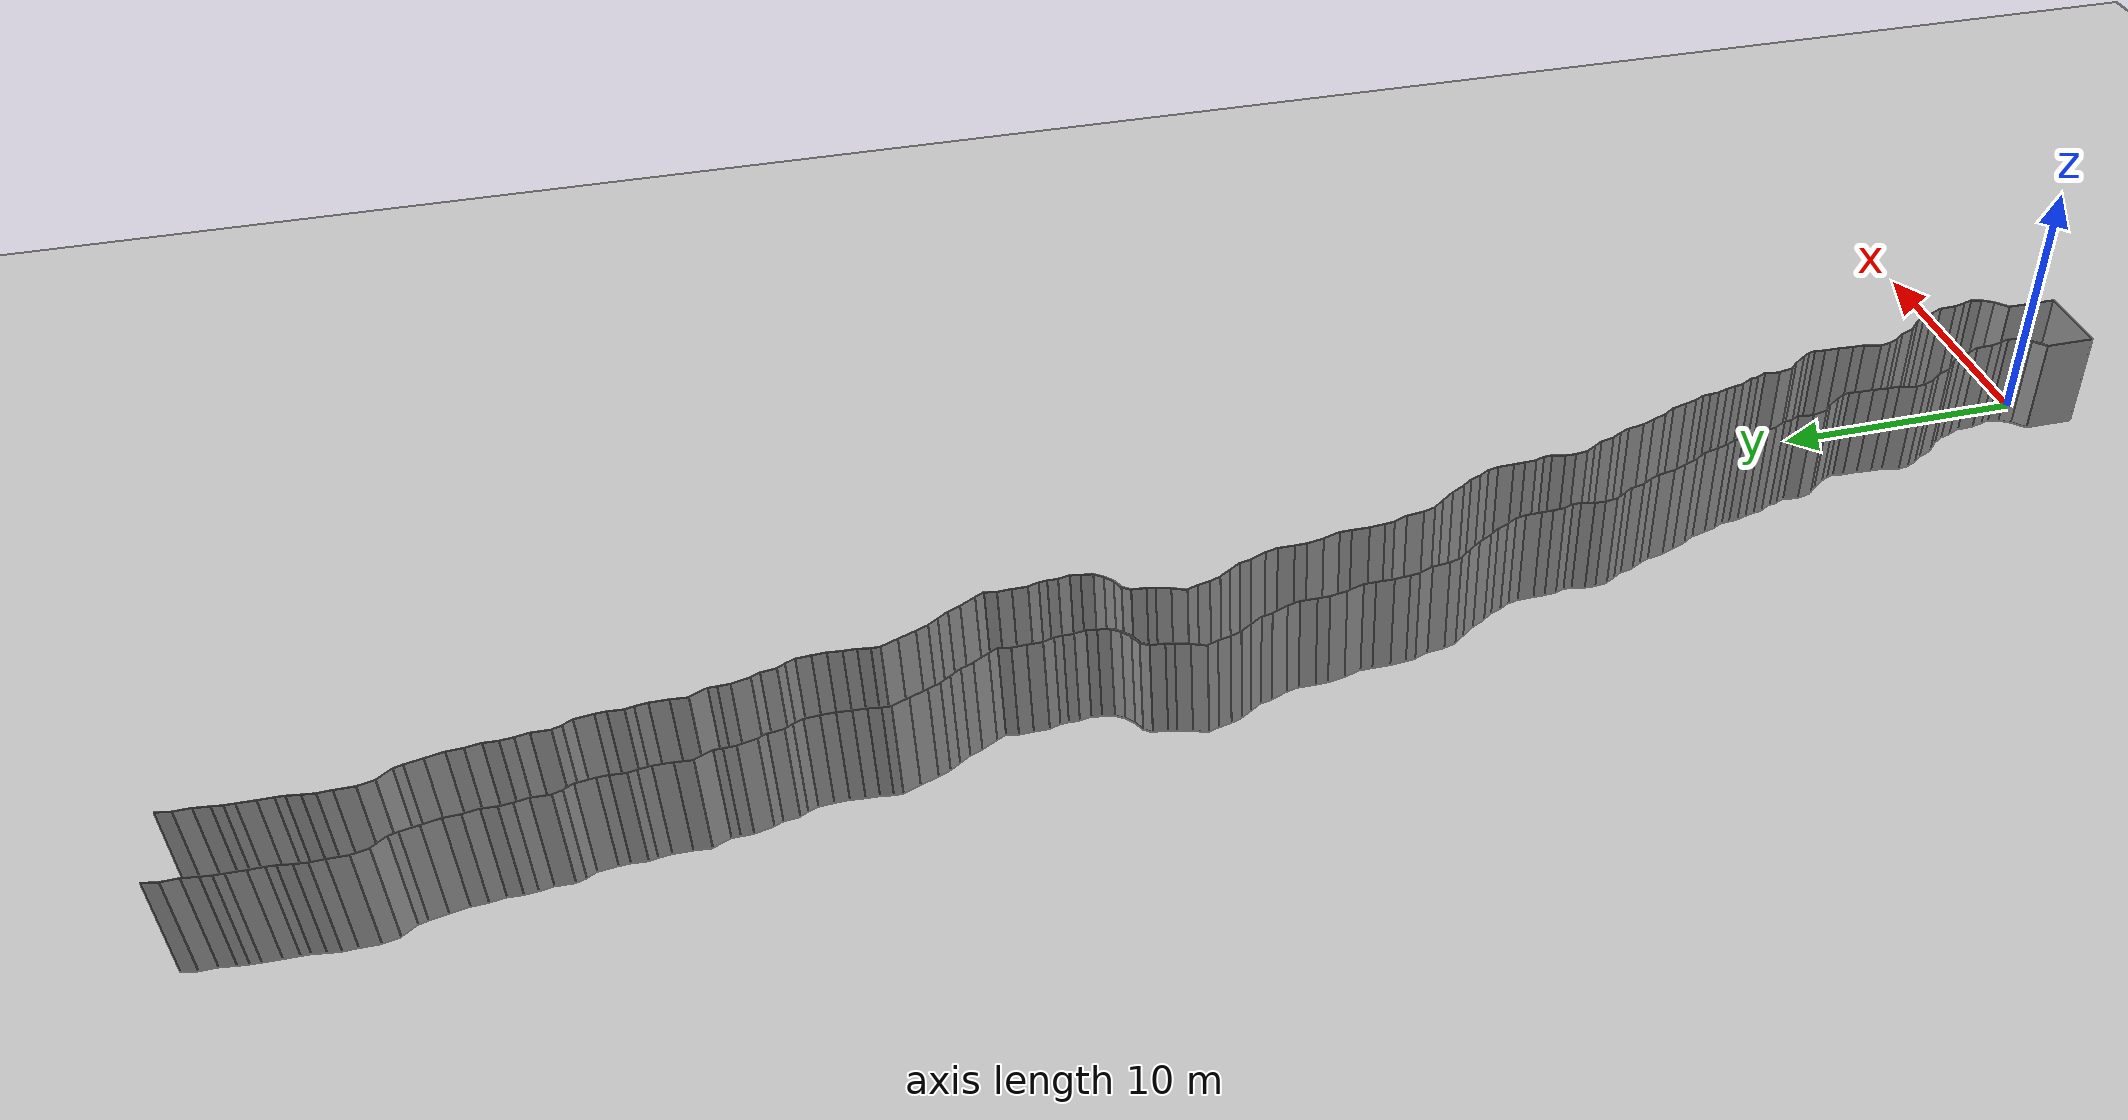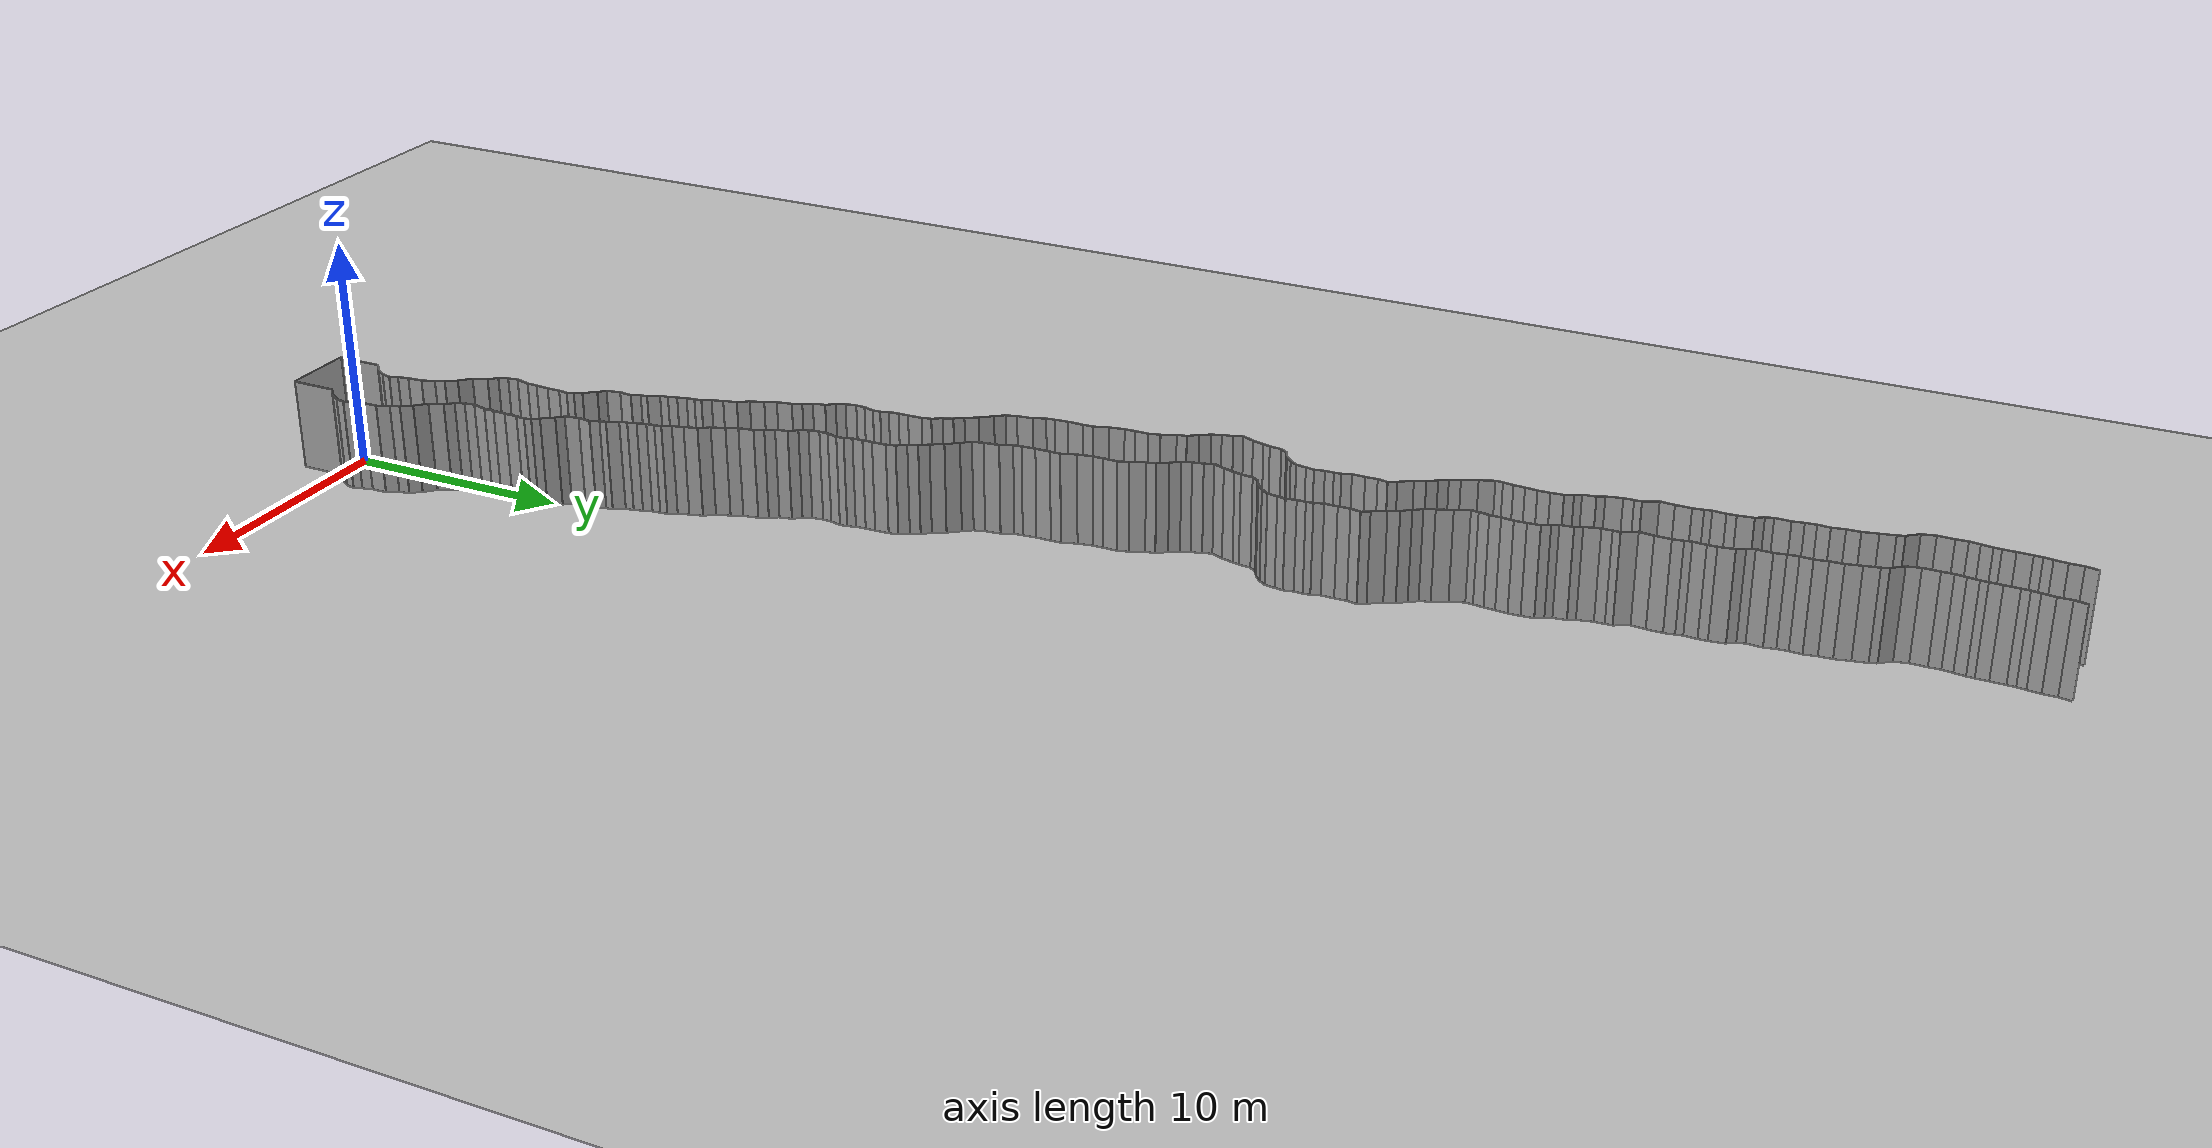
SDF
<sdf version="1.6">
 <world name="default">
  <light name="sun" type="directional">
   <pose>0 0 10 0 -0 0</pose>
   <diffuse>0.8 0.8 0.8 1</diffuse>
   <specular>0.2 0.2 0.2 1</specular>
   <attenuation>
    <range>1000</range>
    <constant>0.9</constant>
    <linear>0.01</linear>
    <quadratic>0.001</quadratic>
   </attenuation>
   <direction>-0.5 0.1 -0.9</direction>
  </light>
  <model name="ground_plane">
   <static>1</static>
   <link name="link">
    <collision name="collision">
     <geometry><plane><normal>0 0 1</normal><size>200 200</size></plane></geometry>
     <surface><friction><ode><mu>100</mu><mu2>50</mu2></ode></friction></surface>
    </collision>
    <visual name="visual">
     <cast_shadows>0</cast_shadows>
     <geometry><plane><normal>0 0 1</normal><size>200 200</size></plane></geometry>
     <material>
      <script><uri>file://media/materials/scripts/gazebo.material</uri><name>Gazebo/Grey</name></script>
     </material>
    </visual>
   </link>
   <pose>0 100 0 0 -0 0</pose>
  </model>
  <gravity>0 0 -9.8</gravity>
  <magnetic_field>6e-06 2.3e-05 -4.2e-05</magnetic_field>
  <atmosphere type="adiabatic"/>
  <physics default="0" name="default_physics" type="ode">
   <max_step_size>0.001</max_step_size>
   <real_time_factor>1</real_time_factor>
   <real_time_update_rate>1000</real_time_update_rate>
  </physics>
  <scene><ambient>0.4 0.4 0.4 1</ambient><background>0.7 0.7 0.7 1</background><shadows>1</shadows></scene>
  <spherical_coordinates>
   <surface_model>EARTH_WGS84</surface_model>
   <latitude_deg>0</latitude_deg>
   <longitude_deg>0</longitude_deg>
   <elevation>0</elevation>
   <heading_deg>0</heading_deg>
  </spherical_coordinates>
  <model name="wall_back">
   <static>1</static>
   <pose>0.0 -2 2 0.0 0 0.0</pose>
   <link name="link">
    <collision name="collision"><geometry><box><size>3 0.02 4</size></box></geometry></collision>
    <visual name="visual">
     <material>
      <script><name>Gazebo/Grey</name><uri>file://media/materials/scripts/gazebo.material</uri></script>
     </material>
     <geometry><box><size>3 0.02 4</size></box></geometry>
    </visual>
   </link>
  </model>
  <model name="wall_left">
   <static>1</static>
   <pose>1.5 -1 2 0 0 0.00</pose>
   <link name="link">
    <collision name="collision"><geometry><box><size>0.02 2 4</size></box></geometry></collision>
    <visual name="visual">
     <material>
      <script><name>Gazebo/Grey</name><uri>file://media/materials/scripts/gazebo.material</uri></script>
     </material>
     <geometry><box><size>0.02 2 4</size></box></geometry>
    </visual>
   </link>
  </model>
  <model name="wall_right">
   <static>1</static>
   <pose>-1.5 -1 2 0 0 0.00</pose>
   <link name="link">
    <collision name="collision"><geometry><box><size>0.02 2 4</size></box></geometry></collision>
    <visual name="visual">
     <material>
      <script><name>Gazebo/Grey</name><uri>file://media/materials/scripts/gazebo.material</uri></script>
     </material>
     <geometry><box><size>0.02 2 4</size></box></geometry>
    </visual>
   </link>
  </model>
  <model name="wall_0">
   <static>1</static>
   <pose>-1.268546775388856 0.21946874336956915 2 0 0 -0.8119696357127165</pose>
   <link name="link">
    <collision name="collision"><geometry><box><size>0.02 0.637925150779 4</size></box></geometry></collision>
    <visual name="visual">
     <material>
      <script><name>Gazebo/Grey</name><uri>file://media/materials/scripts/gazebo.material</uri></script>
     </material>
     <geometry><box><size>0.02 0.637925150779 4</size></box></geometry>
    </visual>
   </link>
  </model>
  <model name="wall_1">
   <static>1</static>
   <pose>1.731453224611144 0.21946874336956915 2 0 0 -0.8119696357127165</pose>
   <link name="link">
    <collision name="collision"><geometry><box><size>0.02 0.637925150779 4</size></box></geometry></collision>
    <visual name="visual">
     <material>
      <script><name>Gazebo/Grey</name><uri>file://media/materials/scripts/gazebo.material</uri></script>
     </material>
     <geometry><box><size>0.02 0.637925150779 4</size></box></geometry>
    </visual>
   </link>
  </model>
  <model name="wall_2">
   <static>1</static>
   <pose>-0.9040545273559997 0.6517059571103775 2 0 0 -0.5587977806842974</pose>
   <link name="link">
    <collision name="collision"><geometry><box><size>0.02 0.50187569671 4</size></box></geometry></collision>
    <visual name="visual">
     <material>
      <script><name>Gazebo/Grey</name><uri>file://media/materials/scripts/gazebo.material</uri></script>
     </material>
     <geometry><box><size>0.02 0.50187569671 4</size></box></geometry>
    </visual>
   </link>
  </model>
  <model name="wall_3">
   <static>1</static>
   <pose>2.0959454726440003 0.6517059571103775 2 0 0 -0.5587977806842974</pose>
   <link name="link">
    <collision name="collision"><geometry><box><size>0.02 0.50187569671 4</size></box></geometry></collision>
    <visual name="visual">
     <material>
      <script><name>Gazebo/Grey</name><uri>file://media/materials/scripts/gazebo.material</uri></script>
     </material>
     <geometry><box><size>0.02 0.50187569671 4</size></box></geometry>
    </visual>
   </link>
  </model>
  <model name="wall_4">
   <static>1</static>
   <pose>-0.7215741765350594 1.0799409530266342 2 0 0 -0.22555712687251003</pose>
   <link name="link">
    <collision name="collision"><geometry><box><size>0.02 0.442132416751 4</size></box></geometry></collision>
    <visual name="visual">
     <material>
      <script><name>Gazebo/Grey</name><uri>file://media/materials/scripts/gazebo.material</uri></script>
     </material>
     <geometry><box><size>0.02 0.442132416751 4</size></box></geometry>
    </visual>
   </link>
  </model>
  <model name="wall_5">
   <static>1</static>
   <pose>2.2784258234649406 1.0799409530266342 2 0 0 -0.22555712687251003</pose>
   <link name="link">
    <collision name="collision"><geometry><box><size>0.02 0.442132416751 4</size></box></geometry></collision>
    <visual name="visual">
     <material>
      <script><name>Gazebo/Grey</name><uri>file://media/materials/scripts/gazebo.material</uri></script>
     </material>
     <geometry><box><size>0.02 0.442132416751 4</size></box></geometry>
    </visual>
   </link>
  </model>
  <model name="wall_6">
   <static>1</static>
   <pose>-0.7332599195898859 1.4806173207940363 2 0 0 0.318785648126557</pose>
   <link name="link">
    <collision name="collision"><geometry><box><size>0.02 0.390072836267 4</size></box></geometry></collision>
    <visual name="visual">
     <material>
      <script><name>Gazebo/Grey</name><uri>file://media/materials/scripts/gazebo.material</uri></script>
     </material>
     <geometry><box><size>0.02 0.390072836267 4</size></box></geometry>
    </visual>
   </link>
  </model>
  <model name="wall_7">
   <static>1</static>
   <pose>2.266740080410114 1.4806173207940363 2 0 0 0.318785648126557</pose>
   <link name="link">
    <collision name="collision"><geometry><box><size>0.02 0.390072836267 4</size></box></geometry></collision>
    <visual name="visual">
     <material>
      <script><name>Gazebo/Grey</name><uri>file://media/materials/scripts/gazebo.material</uri></script>
     </material>
     <geometry><box><size>0.02 0.390072836267 4</size></box></geometry>
    </visual>
   </link>
  </model>
  <model name="wall_8">
   <static>1</static>
   <pose>-0.8505706344513954 1.8990331960274434 2 0 0 0.2364132621165179</pose>
   <link name="link">
    <collision name="collision"><geometry><box><size>0.02 0.47975683729 4</size></box></geometry></collision>
    <visual name="visual">
     <material>
      <script><name>Gazebo/Grey</name><uri>file://media/materials/scripts/gazebo.material</uri></script>
     </material>
     <geometry><box><size>0.02 0.47975683729 4</size></box></geometry>
    </visual>
   </link>
  </model>
  <model name="wall_9">
   <static>1</static>
   <pose>2.1494293655486048 1.8990331960274434 2 0 0 0.2364132621165179</pose>
   <link name="link">
    <collision name="collision"><geometry><box><size>0.02 0.47975683729 4</size></box></geometry></collision>
    <visual name="visual">
     <material>
      <script><name>Gazebo/Grey</name><uri>file://media/materials/scripts/gazebo.material</uri></script>
     </material>
     <geometry><box><size>0.02 0.47975683729 4</size></box></geometry>
    </visual>
   </link>
  </model>
  <model name="wall_10">
   <static>1</static>
   <pose>-0.9196730757531828 2.473693347514386 2 0 0 0.03781661205570284</pose>
   <link name="link">
    <collision name="collision"><geometry><box><size>0.02 0.683396840313 4</size></box></geometry></collision>
    <visual name="visual">
     <material>
      <script><name>Gazebo/Grey</name><uri>file://media/materials/scripts/gazebo.material</uri></script>
     </material>
     <geometry><box><size>0.02 0.683396840313 4</size></box></geometry>
    </visual>
   </link>
  </model>
  <model name="wall_11">
   <static>1</static>
   <pose>2.080326924246817 2.473693347514386 2 0 0 0.03781661205570284</pose>
   <link name="link">
    <collision name="collision"><geometry><box><size>0.02 0.683396840313 4</size></box></geometry></collision>
    <visual name="visual">
     <material>
      <script><name>Gazebo/Grey</name><uri>file://media/materials/scripts/gazebo.material</uri></script>
     </material>
     <geometry><box><size>0.02 0.683396840313 4</size></box></geometry>
    </visual>
   </link>
  </model>
  <model name="wall_12">
   <static>1</static>
   <pose>-1.0510843043802374 3.0766273766579872 2 0 0 0.42547929488258074</pose>
   <link name="link">
    <collision name="collision"><geometry><box><size>0.02 0.574150503129 4</size></box></geometry></collision>
    <visual name="visual">
     <material>
      <script><name>Gazebo/Grey</name><uri>file://media/materials/scripts/gazebo.material</uri></script>
     </material>
     <geometry><box><size>0.02 0.574150503129 4</size></box></geometry>
    </visual>
   </link>
  </model>
  <model name="wall_13">
   <static>1</static>
   <pose>1.9489156956197626 3.0766273766579872 2 0 0 0.42547929488258074</pose>
   <link name="link">
    <collision name="collision"><geometry><box><size>0.02 0.574150503129 4</size></box></geometry></collision>
    <visual name="visual">
     <material>
      <script><name>Gazebo/Grey</name><uri>file://media/materials/scripts/gazebo.material</uri></script>
     </material>
     <geometry><box><size>0.02 0.574150503129 4</size></box></geometry>
    </visual>
   </link>
  </model>
  <model name="wall_14">
   <static>1</static>
   <pose>-1.2323841443039332 3.551140632230809 2 0 0 0.2867017140573027</pose>
   <link name="link">
    <collision name="collision"><geometry><box><size>0.02 0.444198048466 4</size></box></geometry></collision>
    <visual name="visual">
     <material>
      <script><name>Gazebo/Grey</name><uri>file://media/materials/scripts/gazebo.material</uri></script>
     </material>
     <geometry><box><size>0.02 0.444198048466 4</size></box></geometry>
    </visual>
   </link>
  </model>
  <model name="wall_15">
   <static>1</static>
   <pose>1.7676158556960668 3.551140632230809 2 0 0 0.2867017140573027</pose>
   <link name="link">
    <collision name="collision"><geometry><box><size>0.02 0.444198048466 4</size></box></geometry></collision>
    <visual name="visual">
     <material>
      <script><name>Gazebo/Grey</name><uri>file://media/materials/scripts/gazebo.material</uri></script>
     </material>
     <geometry><box><size>0.02 0.444198048466 4</size></box></geometry>
    </visual>
   </link>
  </model>
  <model name="wall_16">
   <static>1</static>
   <pose>-1.446954385748814 3.9921352371495864 2 0 0 0.5873604989164706</pose>
   <link name="link">
    <collision name="collision"><geometry><box><size>0.02 0.547716326666 4</size></box></geometry></collision>
    <visual name="visual">
     <material>
      <script><name>Gazebo/Grey</name><uri>file://media/materials/scripts/gazebo.material</uri></script>
     </material>
     <geometry><box><size>0.02 0.547716326666 4</size></box></geometry>
    </visual>
   </link>
  </model>
  <model name="wall_17">
   <static>1</static>
   <pose>1.553045614251186 3.9921352371495864 2 0 0 0.5873604989164706</pose>
   <link name="link">
    <collision name="collision"><geometry><box><size>0.02 0.547716326666 4</size></box></geometry></collision>
    <visual name="visual">
     <material>
      <script><name>Gazebo/Grey</name><uri>file://media/materials/scripts/gazebo.material</uri></script>
     </material>
     <geometry><box><size>0.02 0.547716326666 4</size></box></geometry>
    </visual>
   </link>
  </model>
  <model name="wall_18">
   <static>1</static>
   <pose>-1.81945374808341 4.443876371837759 2 0 0 0.7785518512731552</pose>
   <link name="link">
    <collision name="collision"><geometry><box><size>0.02 0.628655860006 4</size></box></geometry></collision>
    <visual name="visual">
     <material>
      <script><name>Gazebo/Grey</name><uri>file://media/materials/scripts/gazebo.material</uri></script>
     </material>
     <geometry><box><size>0.02 0.628655860006 4</size></box></geometry>
    </visual>
   </link>
  </model>
  <model name="wall_19">
   <static>1</static>
   <pose>1.18054625191659 4.443876371837759 2 0 0 0.7785518512731552</pose>
   <link name="link">
    <collision name="collision"><geometry><box><size>0.02 0.628655860006 4</size></box></geometry></collision>
    <visual name="visual">
     <material>
      <script><name>Gazebo/Grey</name><uri>file://media/materials/scripts/gazebo.material</uri></script>
     </material>
     <geometry><box><size>0.02 0.628655860006 4</size></box></geometry>
    </visual>
   </link>
  </model>
  <model name="wall_20">
   <static>1</static>
   <pose>-2.166937635361994 4.964693277102102 2 0 0 0.40331440098982274</pose>
   <link name="link">
    <collision name="collision"><geometry><box><size>0.02 0.645897485215 4</size></box></geometry></collision>
    <visual name="visual">
     <material>
      <script><name>Gazebo/Grey</name><uri>file://media/materials/scripts/gazebo.material</uri></script>
     </material>
     <geometry><box><size>0.02 0.645897485215 4</size></box></geometry>
    </visual>
   </link>
  </model>
  <model name="wall_21">
   <static>1</static>
   <pose>0.833062364638006 4.964693277102102 2 0 0 0.40331440098982274</pose>
   <link name="link">
    <collision name="collision"><geometry><box><size>0.02 0.645897485215 4</size></box></geometry></collision>
    <visual name="visual">
     <material>
      <script><name>Gazebo/Grey</name><uri>file://media/materials/scripts/gazebo.material</uri></script>
     </material>
     <geometry><box><size>0.02 0.645897485215 4</size></box></geometry>
    </visual>
   </link>
  </model>
  <model name="wall_22">
   <static>1</static>
   <pose>-2.4293353268070423 5.4427106422066975 2 0 0 0.6432007472633602</pose>
   <link name="link">
    <collision name="collision"><geometry><box><size>0.02 0.452348955525 4</size></box></geometry></collision>
    <visual name="visual">
     <material>
      <script><name>Gazebo/Grey</name><uri>file://media/materials/scripts/gazebo.material</uri></script>
     </material>
     <geometry><box><size>0.02 0.452348955525 4</size></box></geometry>
    </visual>
   </link>
  </model>
  <model name="wall_23">
   <static>1</static>
   <pose>0.5706646731929577 5.4427106422066975 2 0 0 0.6432007472633602</pose>
   <link name="link">
    <collision name="collision"><geometry><box><size>0.02 0.452348955525 4</size></box></geometry></collision>
    <visual name="visual">
     <material>
      <script><name>Gazebo/Grey</name><uri>file://media/materials/scripts/gazebo.material</uri></script>
     </material>
     <geometry><box><size>0.02 0.452348955525 4</size></box></geometry>
    </visual>
   </link>
  </model>
  <model name="wall_24">
   <static>1</static>
   <pose>-2.649575518176277 5.820467784564643 2 0 0 0.4059943945643651</pose>
   <link name="link">
    <collision name="collision"><geometry><box><size>0.02 0.428376265459 4</size></box></geometry></collision>
    <visual name="visual">
     <material>
      <script><name>Gazebo/Grey</name><uri>file://media/materials/scripts/gazebo.material</uri></script>
     </material>
     <geometry><box><size>0.02 0.428376265459 4</size></box></geometry>
    </visual>
   </link>
  </model>
  <model name="wall_25">
   <static>1</static>
   <pose>0.350424481823723 5.820467784564643 2 0 0 0.4059943945643651</pose>
   <link name="link">
    <collision name="collision"><geometry><box><size>0.02 0.428376265459 4</size></box></geometry></collision>
    <visual name="visual">
     <material>
      <script><name>Gazebo/Grey</name><uri>file://media/materials/scripts/gazebo.material</uri></script>
     </material>
     <geometry><box><size>0.02 0.428376265459 4</size></box></geometry>
    </visual>
   </link>
  </model>
  <model name="wall_26">
   <static>1</static>
   <pose>-2.7732187405365583 6.237583993818234 2 0 0 0.1754200736375513</pose>
   <link name="link">
    <collision name="collision"><geometry><box><size>0.02 0.447547168787 4</size></box></geometry></collision>
    <visual name="visual">
     <material>
      <script><name>Gazebo/Grey</name><uri>file://media/materials/scripts/gazebo.material</uri></script>
     </material>
     <geometry><box><size>0.02 0.447547168787 4</size></box></geometry>
    </visual>
   </link>
  </model>
  <model name="wall_27">
   <static>1</static>
   <pose>0.22678125946344174 6.237583993818234 2 0 0 0.1754200736375513</pose>
   <link name="link">
    <collision name="collision"><geometry><box><size>0.02 0.447547168787 4</size></box></geometry></collision>
    <visual name="visual">
     <material>
      <script><name>Gazebo/Grey</name><uri>file://media/materials/scripts/gazebo.material</uri></script>
     </material>
     <geometry><box><size>0.02 0.447547168787 4</size></box></geometry>
    </visual>
   </link>
  </model>
  <model name="wall_28">
   <static>1</static>
   <pose>-2.7248131909323514 6.7846727944053855 2 0 0 -0.26153288845329814</pose>
   <link name="link">
    <collision name="collision"><geometry><box><size>0.02 0.676503455935 4</size></box></geometry></collision>
    <visual name="visual">
     <material>
      <script><name>Gazebo/Grey</name><uri>file://media/materials/scripts/gazebo.material</uri></script>
     </material>
     <geometry><box><size>0.02 0.676503455935 4</size></box></geometry>
    </visual>
   </link>
  </model>
  <model name="wall_29">
   <static>1</static>
   <pose>0.2751868090676486 6.7846727944053855 2 0 0 -0.26153288845329814</pose>
   <link name="link">
    <collision name="collision"><geometry><box><size>0.02 0.676503455935 4</size></box></geometry></collision>
    <visual name="visual">
     <material>
      <script><name>Gazebo/Grey</name><uri>file://media/materials/scripts/gazebo.material</uri></script>
     </material>
     <geometry><box><size>0.02 0.676503455935 4</size></box></geometry>
    </visual>
   </link>
  </model>
  <model name="wall_30">
   <static>1</static>
   <pose>-2.6326140372152835 7.345889244844755 2 0 0 -0.02021432939373362</pose>
   <link name="link">
    <collision name="collision"><geometry><box><size>0.02 0.469029926559 4</size></box></geometry></collision>
    <visual name="visual">
     <material>
      <script><name>Gazebo/Grey</name><uri>file://media/materials/scripts/gazebo.material</uri></script>
     </material>
     <geometry><box><size>0.02 0.469029926559 4</size></box></geometry>
    </visual>
   </link>
  </model>
  <model name="wall_31">
   <static>1</static>
   <pose>0.36738596278471647 7.345889244844755 2 0 0 -0.02021432939373362</pose>
   <link name="link">
    <collision name="collision"><geometry><box><size>0.02 0.469029926559 4</size></box></geometry></collision>
    <visual name="visual">
     <material>
      <script><name>Gazebo/Grey</name><uri>file://media/materials/scripts/gazebo.material</uri></script>
     </material>
     <geometry><box><size>0.02 0.469029926559 4</size></box></geometry>
    </visual>
   </link>
  </model>
  <model name="wall_32">
   <static>1</static>
   <pose>-2.605728959813212 7.885590306142588 2 0 0 -0.07242347026716565</pose>
   <link name="link">
    <collision name="collision"><geometry><box><size>0.02 0.612072527439 4</size></box></geometry></collision>
    <visual name="visual">
     <material>
      <script><name>Gazebo/Grey</name><uri>file://media/materials/scripts/gazebo.material</uri></script>
     </material>
     <geometry><box><size>0.02 0.612072527439 4</size></box></geometry>
    </visual>
   </link>
  </model>
  <model name="wall_33">
   <static>1</static>
   <pose>0.39427104018678794 7.885590306142588 2 0 0 -0.07242347026716565</pose>
   <link name="link">
    <collision name="collision"><geometry><box><size>0.02 0.612072527439 4</size></box></geometry></collision>
    <visual name="visual">
     <material>
      <script><name>Gazebo/Grey</name><uri>file://media/materials/scripts/gazebo.material</uri></script>
     </material>
     <geometry><box><size>0.02 0.612072527439 4</size></box></geometry>
    </visual>
   </link>
  </model>
  <model name="wall_34">
   <static>1</static>
   <pose>-2.5823764355351 8.487993178296218 2 0 0 -0.004063952372006906</pose>
   <link name="link">
    <collision name="collision"><geometry><box><size>0.02 0.594342632225 4</size></box></geometry></collision>
    <visual name="visual">
     <material>
      <script><name>Gazebo/Grey</name><uri>file://media/materials/scripts/gazebo.material</uri></script>
     </material>
     <geometry><box><size>0.02 0.594342632225 4</size></box></geometry>
    </visual>
   </link>
  </model>
  <model name="wall_35">
   <static>1</static>
   <pose>0.4176235644649 8.487993178296218 2 0 0 -0.004063952372006906</pose>
   <link name="link">
    <collision name="collision"><geometry><box><size>0.02 0.594342632225 4</size></box></geometry></collision>
    <visual name="visual">
     <material>
      <script><name>Gazebo/Grey</name><uri>file://media/materials/scripts/gazebo.material</uri></script>
     </material>
     <geometry><box><size>0.02 0.594342632225 4</size></box></geometry>
    </visual>
   </link>
  </model>
  <model name="wall_36">
   <static>1</static>
   <pose>-2.554407671798095 8.997587530809655 2 0 0 -0.12531847427243922</pose>
   <link name="link">
    <collision name="collision"><geometry><box><size>0.02 0.428209034052 4</size></box></geometry></collision>
    <visual name="visual">
     <material>
      <script><name>Gazebo/Grey</name><uri>file://media/materials/scripts/gazebo.material</uri></script>
     </material>
     <geometry><box><size>0.02 0.428209034052 4</size></box></geometry>
    </visual>
   </link>
  </model>
  <model name="wall_37">
   <static>1</static>
   <pose>0.4455923282019052 8.997587530809655 2 0 0 -0.12531847427243922</pose>
   <link name="link">
    <collision name="collision"><geometry><box><size>0.02 0.428209034052 4</size></box></geometry></collision>
    <visual name="visual">
     <material>
      <script><name>Gazebo/Grey</name><uri>file://media/materials/scripts/gazebo.material</uri></script>
     </material>
     <geometry><box><size>0.02 0.428209034052 4</size></box></geometry>
    </visual>
   </link>
  </model>
  <model name="wall_38">
   <static>1</static>
   <pose>-2.573418172815218 9.356826306531701 2 0 0 0.30221719389149426</pose>
   <link name="link">
    <collision name="collision"><geometry><box><size>0.02 0.307565785493 4</size></box></geometry></collision>
    <visual name="visual">
     <material>
      <script><name>Gazebo/Grey</name><uri>file://media/materials/scripts/gazebo.material</uri></script>
     </material>
     <geometry><box><size>0.02 0.307565785493 4</size></box></geometry>
    </visual>
   </link>
  </model>
  <model name="wall_39">
   <static>1</static>
   <pose>0.4265818271847821 9.356826306531701 2 0 0 0.30221719389149426</pose>
   <link name="link">
    <collision name="collision"><geometry><box><size>0.02 0.307565785493 4</size></box></geometry></collision>
    <visual name="visual">
     <material>
      <script><name>Gazebo/Grey</name><uri>file://media/materials/scripts/gazebo.material</uri></script>
     </material>
     <geometry><box><size>0.02 0.307565785493 4</size></box></geometry>
    </visual>
   </link>
  </model>
  <model name="wall_40">
   <static>1</static>
   <pose>-2.7092129441926875 9.659572125686658 2 0 0 0.5235771457483689</pose>
   <link name="link">
    <collision name="collision"><geometry><box><size>0.02 0.360106264601 4</size></box></geometry></collision>
    <visual name="visual">
     <material>
      <script><name>Gazebo/Grey</name><uri>file://media/materials/scripts/gazebo.material</uri></script>
     </material>
     <geometry><box><size>0.02 0.360106264601 4</size></box></geometry>
    </visual>
   </link>
  </model>
  <model name="wall_41">
   <static>1</static>
   <pose>0.29078705580731246 9.659572125686658 2 0 0 0.5235771457483689</pose>
   <link name="link">
    <collision name="collision"><geometry><box><size>0.02 0.360106264601 4</size></box></geometry></collision>
    <visual name="visual">
     <material>
      <script><name>Gazebo/Grey</name><uri>file://media/materials/scripts/gazebo.material</uri></script>
     </material>
     <geometry><box><size>0.02 0.360106264601 4</size></box></geometry>
    </visual>
   </link>
  </model>
  <model name="wall_42">
   <static>1</static>
   <pose>-2.97848362910238 10.070076589667385 2 0 0 0.6134812625743524</pose>
   <link name="link">
    <collision name="collision"><geometry><box><size>0.02 0.62269263957 4</size></box></geometry></collision>
    <visual name="visual">
     <material>
      <script><name>Gazebo/Grey</name><uri>file://media/materials/scripts/gazebo.material</uri></script>
     </material>
     <geometry><box><size>0.02 0.62269263957 4</size></box></geometry>
    </visual>
   </link>
  </model>
  <model name="wall_43">
   <static>1</static>
   <pose>0.02151637089761982 10.070076589667385 2 0 0 0.6134812625743524</pose>
   <link name="link">
    <collision name="collision"><geometry><box><size>0.02 0.62269263957 4</size></box></geometry></collision>
    <visual name="visual">
     <material>
      <script><name>Gazebo/Grey</name><uri>file://media/materials/scripts/gazebo.material</uri></script>
     </material>
     <geometry><box><size>0.02 0.62269263957 4</size></box></geometry>
    </visual>
   </link>
  </model>
  <model name="wall_44">
   <static>1</static>
   <pose>-3.2922154291811276 10.467831383368289 2 0 0 0.7540811336149634</pose>
   <link name="link">
    <collision name="collision"><geometry><box><size>0.02 0.392873321355 4</size></box></geometry></collision>
    <visual name="visual">
     <material>
      <script><name>Gazebo/Grey</name><uri>file://media/materials/scripts/gazebo.material</uri></script>
     </material>
     <geometry><box><size>0.02 0.392873321355 4</size></box></geometry>
    </visual>
   </link>
  </model>
  <model name="wall_45">
   <static>1</static>
   <pose>-0.29221542918112764 10.467831383368289 2 0 0 0.7540811336149634</pose>
   <link name="link">
    <collision name="collision"><geometry><box><size>0.02 0.392873321355 4</size></box></geometry></collision>
    <visual name="visual">
     <material>
      <script><name>Gazebo/Grey</name><uri>file://media/materials/scripts/gazebo.material</uri></script>
     </material>
     <geometry><box><size>0.02 0.392873321355 4</size></box></geometry>
    </visual>
   </link>
  </model>
  <model name="wall_46">
   <static>1</static>
   <pose>-3.4960749040405514 10.913240104627954 2 0 0 0.22563850545443595</pose>
   <link name="link">
    <collision name="collision"><geometry><box><size>0.02 0.620172178579 4</size></box></geometry></collision>
    <visual name="visual">
     <material>
      <script><name>Gazebo/Grey</name><uri>file://media/materials/scripts/gazebo.material</uri></script>
     </material>
     <geometry><box><size>0.02 0.620172178579 4</size></box></geometry>
    </visual>
   </link>
  </model>
  <model name="wall_47">
   <static>1</static>
   <pose>-0.49607490404055143 10.913240104627954 2 0 0 0.22563850545443595</pose>
   <link name="link">
    <collision name="collision"><geometry><box><size>0.02 0.620172178579 4</size></box></geometry></collision>
    <visual name="visual">
     <material>
      <script><name>Gazebo/Grey</name><uri>file://media/materials/scripts/gazebo.material</uri></script>
     </material>
     <geometry><box><size>0.02 0.620172178579 4</size></box></geometry>
    </visual>
   </link>
  </model>
  <model name="wall_48">
   <static>1</static>
   <pose>-3.5227978954640142 11.513726871136802 2 0 0 -0.1420398936168532</pose>
   <link name="link">
    <collision name="collision"><geometry><box><size>0.02 0.602590334272 4</size></box></geometry></collision>
    <visual name="visual">
     <material>
      <script><name>Gazebo/Grey</name><uri>file://media/materials/scripts/gazebo.material</uri></script>
     </material>
     <geometry><box><size>0.02 0.602590334272 4</size></box></geometry>
    </visual>
   </link>
  </model>
  <model name="wall_49">
   <static>1</static>
   <pose>-0.5227978954640142 11.513726871136802 2 0 0 -0.1420398936168532</pose>
   <link name="link">
    <collision name="collision"><geometry><box><size>0.02 0.602590334272 4</size></box></geometry></collision>
    <visual name="visual">
     <material>
      <script><name>Gazebo/Grey</name><uri>file://media/materials/scripts/gazebo.material</uri></script>
     </material>
     <geometry><box><size>0.02 0.602590334272 4</size></box></geometry>
    </visual>
   </link>
  </model>
  <model name="wall_50">
   <static>1</static>
   <pose>-3.574038922288434 11.997799308946025 2 0 0 0.46788991533035973</pose>
   <link name="link">
    <collision name="collision"><geometry><box><size>0.02 0.416374147336 4</size></box></geometry></collision>
    <visual name="visual">
     <material>
      <script><name>Gazebo/Grey</name><uri>file://media/materials/scripts/gazebo.material</uri></script>
     </material>
     <geometry><box><size>0.02 0.416374147336 4</size></box></geometry>
    </visual>
   </link>
  </model>
  <model name="wall_51">
   <static>1</static>
   <pose>-0.5740389222884339 11.997799308946025 2 0 0 0.46788991533035973</pose>
   <link name="link">
    <collision name="collision"><geometry><box><size>0.02 0.416374147336 4</size></box></geometry></collision>
    <visual name="visual">
     <material>
      <script><name>Gazebo/Grey</name><uri>file://media/materials/scripts/gazebo.material</uri></script>
     </material>
     <geometry><box><size>0.02 0.416374147336 4</size></box></geometry>
    </visual>
   </link>
  </model>
  <model name="wall_52">
   <static>1</static>
   <pose>-3.684685031745664 12.33310087231097 2 0 0 0.11160140679598836</pose>
   <link name="link">
    <collision name="collision"><geometry><box><size>0.02 0.300851659717 4</size></box></geometry></collision>
    <visual name="visual">
     <material>
      <script><name>Gazebo/Grey</name><uri>file://media/materials/scripts/gazebo.material</uri></script>
     </material>
     <geometry><box><size>0.02 0.300851659717 4</size></box></geometry>
    </visual>
   </link>
  </model>
  <model name="wall_53">
   <static>1</static>
   <pose>-0.6846850317456639 12.33310087231097 2 0 0 0.11160140679598836</pose>
   <link name="link">
    <collision name="collision"><geometry><box><size>0.02 0.300851659717 4</size></box></geometry></collision>
    <visual name="visual">
     <material>
      <script><name>Gazebo/Grey</name><uri>file://media/materials/scripts/gazebo.material</uri></script>
     </material>
     <geometry><box><size>0.02 0.300851659717 4</size></box></geometry>
    </visual>
   </link>
  </model>
  <model name="wall_54">
   <static>1</static>
   <pose>-3.835509610672219 12.720199287340694 2 0 0 0.5137214898504788</pose>
   <link name="link">
    <collision name="collision"><geometry><box><size>0.02 0.545648075531 4</size></box></geometry></collision>
    <visual name="visual">
     <material>
      <script><name>Gazebo/Grey</name><uri>file://media/materials/scripts/gazebo.material</uri></script>
     </material>
     <geometry><box><size>0.02 0.545648075531 4</size></box></geometry>
    </visual>
   </link>
  </model>
  <model name="wall_55">
   <static>1</static>
   <pose>-0.8355096106722191 12.720199287340694 2 0 0 0.5137214898504788</pose>
   <link name="link">
    <collision name="collision"><geometry><box><size>0.02 0.545648075531 4</size></box></geometry></collision>
    <visual name="visual">
     <material>
      <script><name>Gazebo/Grey</name><uri>file://media/materials/scripts/gazebo.material</uri></script>
     </material>
     <geometry><box><size>0.02 0.545648075531 4</size></box></geometry>
    </visual>
   </link>
  </model>
  <model name="wall_56">
   <static>1</static>
   <pose>-3.998458795984539 13.135990927488207 2 0 0 0.16066940188695944</pose>
   <link name="link">
    <collision name="collision"><geometry><box><size>0.02 0.36101625879 4</size></box></geometry></collision>
    <visual name="visual">
     <material>
      <script><name>Gazebo/Grey</name><uri>file://media/materials/scripts/gazebo.material</uri></script>
     </material>
     <geometry><box><size>0.02 0.36101625879 4</size></box></geometry>
    </visual>
   </link>
  </model>
  <model name="wall_57">
   <static>1</static>
   <pose>-0.998458795984539 13.135990927488207 2 0 0 0.16066940188695944</pose>
   <link name="link">
    <collision name="collision"><geometry><box><size>0.02 0.36101625879 4</size></box></geometry></collision>
    <visual name="visual">
     <material>
      <script><name>Gazebo/Grey</name><uri>file://media/materials/scripts/gazebo.material</uri></script>
     </material>
     <geometry><box><size>0.02 0.36101625879 4</size></box></geometry>
    </visual>
   </link>
  </model>
  <model name="wall_58">
   <static>1</static>
   <pose>-4.080508287782165 13.51105411846598 2 0 0 0.26377998638756905</pose>
   <link name="link">
    <collision name="collision"><geometry><box><size>0.02 0.407867462001 4</size></box></geometry></collision>
    <visual name="visual">
     <material>
      <script><name>Gazebo/Grey</name><uri>file://media/materials/scripts/gazebo.material</uri></script>
     </material>
     <geometry><box><size>0.02 0.407867462001 4</size></box></geometry>
    </visual>
   </link>
  </model>
  <model name="wall_59">
   <static>1</static>
   <pose>-1.0805082877821652 13.51105411846598 2 0 0 0.26377998638756905</pose>
   <link name="link">
    <collision name="collision"><geometry><box><size>0.02 0.407867462001 4</size></box></geometry></collision>
    <visual name="visual">
     <material>
      <script><name>Gazebo/Grey</name><uri>file://media/materials/scripts/gazebo.material</uri></script>
     </material>
     <geometry><box><size>0.02 0.407867462001 4</size></box></geometry>
    </visual>
   </link>
  </model>
  <model name="wall_60">
   <static>1</static>
   <pose>-4.196516012435625 13.90495863176452 2 0 0 0.30872603140242194</pose>
   <link name="link">
    <collision name="collision"><geometry><box><size>0.02 0.413603756892 4</size></box></geometry></collision>
    <visual name="visual">
     <material>
      <script><name>Gazebo/Grey</name><uri>file://media/materials/scripts/gazebo.material</uri></script>
     </material>
     <geometry><box><size>0.02 0.413603756892 4</size></box></geometry>
    </visual>
   </link>
  </model>
  <model name="wall_61">
   <static>1</static>
   <pose>-1.1965160124356249 13.90495863176452 2 0 0 0.30872603140242194</pose>
   <link name="link">
    <collision name="collision"><geometry><box><size>0.02 0.413603756892 4</size></box></geometry></collision>
    <visual name="visual">
     <material>
      <script><name>Gazebo/Grey</name><uri>file://media/materials/scripts/gazebo.material</uri></script>
     </material>
     <geometry><box><size>0.02 0.413603756892 4</size></box></geometry>
    </visual>
   </link>
  </model>
  <model name="wall_62">
   <static>1</static>
   <pose>-4.273051628968552 14.285547763 2 0 0 0.07449433003170143</pose>
   <link name="link">
    <collision name="collision"><geometry><box><size>0.02 0.368150133713 4</size></box></geometry></collision>
    <visual name="visual">
     <material>
      <script><name>Gazebo/Grey</name><uri>file://media/materials/scripts/gazebo.material</uri></script>
     </material>
     <geometry><box><size>0.02 0.368150133713 4</size></box></geometry>
    </visual>
   </link>
  </model>
  <model name="wall_63">
   <static>1</static>
   <pose>-1.2730516289685516 14.285547763 2 0 0 0.07449433003170143</pose>
   <link name="link">
    <collision name="collision"><geometry><box><size>0.02 0.368150133713 4</size></box></geometry></collision>
    <visual name="visual">
     <material>
      <script><name>Gazebo/Grey</name><uri>file://media/materials/scripts/gazebo.material</uri></script>
     </material>
     <geometry><box><size>0.02 0.368150133713 4</size></box></geometry>
    </visual>
   </link>
  </model>
  <model name="wall_64">
   <static>1</static>
   <pose>-4.306963320157503 14.630731096822434 2 0 0 0.12441270922051477</pose>
   <link name="link">
    <collision name="collision"><geometry><box><size>0.02 0.325755424808 4</size></box></geometry></collision>
    <visual name="visual">
     <material>
      <script><name>Gazebo/Grey</name><uri>file://media/materials/scripts/gazebo.material</uri></script>
     </material>
     <geometry><box><size>0.02 0.325755424808 4</size></box></geometry>
    </visual>
   </link>
  </model>
  <model name="wall_65">
   <static>1</static>
   <pose>-1.3069633201575028 14.630731096822434 2 0 0 0.12441270922051477</pose>
   <link name="link">
    <collision name="collision"><geometry><box><size>0.02 0.325755424808 4</size></box></geometry></collision>
    <visual name="visual">
     <material>
      <script><name>Gazebo/Grey</name><uri>file://media/materials/scripts/gazebo.material</uri></script>
     </material>
     <geometry><box><size>0.02 0.325755424808 4</size></box></geometry>
    </visual>
   </link>
  </model>
  <model name="wall_66">
   <static>1</static>
   <pose>-4.425348202243941 14.984295278831334 2 0 0 0.47277627727432797</pose>
   <link name="link">
    <collision name="collision"><geometry><box><size>0.02 0.431188986267 4</size></box></geometry></collision>
    <visual name="visual">
     <material>
      <script><name>Gazebo/Grey</name><uri>file://media/materials/scripts/gazebo.material</uri></script>
     </material>
     <geometry><box><size>0.02 0.431188986267 4</size></box></geometry>
    </visual>
   </link>
  </model>
  <model name="wall_67">
   <static>1</static>
   <pose>-1.4253482022439412 14.984295278831334 2 0 0 0.47277627727432797</pose>
   <link name="link">
    <collision name="collision"><geometry><box><size>0.02 0.431188986267 4</size></box></geometry></collision>
    <visual name="visual">
     <material>
      <script><name>Gazebo/Grey</name><uri>file://media/materials/scripts/gazebo.material</uri></script>
     </material>
     <geometry><box><size>0.02 0.431188986267 4</size></box></geometry>
    </visual>
   </link>
  </model>
  <model name="wall_68">
   <static>1</static>
   <pose>-4.593763483631637 15.419056577256672 2 0 0 0.28159481010173315</pose>
   <link name="link">
    <collision name="collision"><geometry><box><size>0.02 0.505543395887 4</size></box></geometry></collision>
    <visual name="visual">
     <material>
      <script><name>Gazebo/Grey</name><uri>file://media/materials/scripts/gazebo.material</uri></script>
     </material>
     <geometry><box><size>0.02 0.505543395887 4</size></box></geometry>
    </visual>
   </link>
  </model>
  <model name="wall_69">
   <static>1</static>
   <pose>-1.593763483631637 15.419056577256672 2 0 0 0.28159481010173315</pose>
   <link name="link">
    <collision name="collision"><geometry><box><size>0.02 0.505543395887 4</size></box></geometry></collision>
    <visual name="visual">
     <material>
      <script><name>Gazebo/Grey</name><uri>file://media/materials/scripts/gazebo.material</uri></script>
     </material>
     <geometry><box><size>0.02 0.505543395887 4</size></box></geometry>
    </visual>
   </link>
  </model>
  <model name="wall_70">
   <static>1</static>
   <pose>-4.739704616200733 15.950339871127522 2 0 0 0.2566312104398875</pose>
   <link name="link">
    <collision name="collision"><geometry><box><size>0.02 0.596468815916 4</size></box></geometry></collision>
    <visual name="visual">
     <material>
      <script><name>Gazebo/Grey</name><uri>file://media/materials/scripts/gazebo.material</uri></script>
     </material>
     <geometry><box><size>0.02 0.596468815916 4</size></box></geometry>
    </visual>
   </link>
  </model>
  <model name="wall_71">
   <static>1</static>
   <pose>-1.7397046162007328 15.950339871127522 2 0 0 0.2566312104398875</pose>
   <link name="link">
    <collision name="collision"><geometry><box><size>0.02 0.596468815916 4</size></box></geometry></collision>
    <visual name="visual">
     <material>
      <script><name>Gazebo/Grey</name><uri>file://media/materials/scripts/gazebo.material</uri></script>
     </material>
     <geometry><box><size>0.02 0.596468815916 4</size></box></geometry>
    </visual>
   </link>
  </model>
  <model name="wall_72">
   <static>1</static>
   <pose>-4.963111926831633 16.465281734666583 2 0 0 0.5779256583100791</pose>
   <link name="link">
    <collision name="collision"><geometry><box><size>0.02 0.540771511479 4</size></box></geometry></collision>
    <visual name="visual">
     <material>
      <script><name>Gazebo/Grey</name><uri>file://media/materials/scripts/gazebo.material</uri></script>
     </material>
     <geometry><box><size>0.02 0.540771511479 4</size></box></geometry>
    </visual>
   </link>
  </model>
  <model name="wall_73">
   <static>1</static>
   <pose>-1.9631119268316333 16.465281734666583 2 0 0 0.5779256583100791</pose>
   <link name="link">
    <collision name="collision"><geometry><box><size>0.02 0.540771511479 4</size></box></geometry></collision>
    <visual name="visual">
     <material>
      <script><name>Gazebo/Grey</name><uri>file://media/materials/scripts/gazebo.material</uri></script>
     </material>
     <geometry><box><size>0.02 0.540771511479 4</size></box></geometry>
    </visual>
   </link>
  </model>
  <model name="wall_74">
   <static>1</static>
   <pose>-5.2189894164467265 16.98038068064487 2 0 0 0.3585729482220448</pose>
   <link name="link">
    <collision name="collision"><geometry><box><size>0.02 0.616456454361 4</size></box></geometry></collision>
    <visual name="visual">
     <material>
      <script><name>Gazebo/Grey</name><uri>file://media/materials/scripts/gazebo.material</uri></script>
     </material>
     <geometry><box><size>0.02 0.616456454361 4</size></box></geometry>
    </visual>
   </link>
  </model>
  <model name="wall_75">
   <static>1</static>
   <pose>-2.2189894164467265 16.98038068064487 2 0 0 0.3585729482220448</pose>
   <link name="link">
    <collision name="collision"><geometry><box><size>0.02 0.616456454361 4</size></box></geometry></collision>
    <visual name="visual">
     <material>
      <script><name>Gazebo/Grey</name><uri>file://media/materials/scripts/gazebo.material</uri></script>
     </material>
     <geometry><box><size>0.02 0.616456454361 4</size></box></geometry>
    </visual>
   </link>
  </model>
  <model name="wall_76">
   <static>1</static>
   <pose>-5.429013634270137 17.51802696399884 2 0 0 0.388258755482311</pose>
   <link name="link">
    <collision name="collision"><geometry><box><size>0.02 0.538094146848 4</size></box></geometry></collision>
    <visual name="visual">
     <material>
      <script><name>Gazebo/Grey</name><uri>file://media/materials/scripts/gazebo.material</uri></script>
     </material>
     <geometry><box><size>0.02 0.538094146848 4</size></box></geometry>
    </visual>
   </link>
  </model>
  <model name="wall_77">
   <static>1</static>
   <pose>-2.429013634270137 17.51802696399884 2 0 0 0.388258755482311</pose>
   <link name="link">
    <collision name="collision"><geometry><box><size>0.02 0.538094146848 4</size></box></geometry></collision>
    <visual name="visual">
     <material>
      <script><name>Gazebo/Grey</name><uri>file://media/materials/scripts/gazebo.material</uri></script>
     </material>
     <geometry><box><size>0.02 0.538094146848 4</size></box></geometry>
    </visual>
   </link>
  </model>
  <model name="wall_78">
   <static>1</static>
   <pose>-5.592238927250983 18.094138129854752 2 0 0 0.185468775733689</pose>
   <link name="link">
    <collision name="collision"><geometry><box><size>0.02 0.665593706025 4</size></box></geometry></collision>
    <visual name="visual">
     <material>
      <script><name>Gazebo/Grey</name><uri>file://media/materials/scripts/gazebo.material</uri></script>
     </material>
     <geometry><box><size>0.02 0.665593706025 4</size></box></geometry>
    </visual>
   </link>
  </model>
  <model name="wall_79">
   <static>1</static>
   <pose>-2.5922389272509827 18.094138129854752 2 0 0 0.185468775733689</pose>
   <link name="link">
    <collision name="collision"><geometry><box><size>0.02 0.665593706025 4</size></box></geometry></collision>
    <visual name="visual">
     <material>
      <script><name>Gazebo/Grey</name><uri>file://media/materials/scripts/gazebo.material</uri></script>
     </material>
     <geometry><box><size>0.02 0.665593706025 4</size></box></geometry>
    </visual>
   </link>
  </model>
  <model name="wall_80">
   <static>1</static>
   <pose>-5.744420689968435 18.62157502755074 2 0 0 0.4255702106414798</pose>
   <link name="link">
    <collision name="collision"><geometry><box><size>0.02 0.439935826207 4</size></box></geometry></collision>
    <visual name="visual">
     <material>
      <script><name>Gazebo/Grey</name><uri>file://media/materials/scripts/gazebo.material</uri></script>
     </material>
     <geometry><box><size>0.02 0.439935826207 4</size></box></geometry>
    </visual>
   </link>
  </model>
  <model name="wall_81">
   <static>1</static>
   <pose>-2.744420689968435 18.62157502755074 2 0 0 0.4255702106414798</pose>
   <link name="link">
    <collision name="collision"><geometry><box><size>0.02 0.439935826207 4</size></box></geometry></collision>
    <visual name="visual">
     <material>
      <script><name>Gazebo/Grey</name><uri>file://media/materials/scripts/gazebo.material</uri></script>
     </material>
     <geometry><box><size>0.02 0.439935826207 4</size></box></geometry>
    </visual>
   </link>
  </model>
  <model name="wall_82">
   <static>1</static>
   <pose>-5.946961796509764 19.01404491307644 2 0 0 0.5267457993279648</pose>
   <link name="link">
    <collision name="collision"><geometry><box><size>0.02 0.444497374967 4</size></box></geometry></collision>
    <visual name="visual">
     <material>
      <script><name>Gazebo/Grey</name><uri>file://media/materials/scripts/gazebo.material</uri></script>
     </material>
     <geometry><box><size>0.02 0.444497374967 4</size></box></geometry>
    </visual>
   </link>
  </model>
  <model name="wall_83">
   <static>1</static>
   <pose>-2.946961796509764 19.01404491307644 2 0 0 0.5267457993279648</pose>
   <link name="link">
    <collision name="collision"><geometry><box><size>0.02 0.444497374967 4</size></box></geometry></collision>
    <visual name="visual">
     <material>
      <script><name>Gazebo/Grey</name><uri>file://media/materials/scripts/gazebo.material</uri></script>
     </material>
     <geometry><box><size>0.02 0.444497374967 4</size></box></geometry>
    </visual>
   </link>
  </model>
  <model name="wall_84">
   <static>1</static>
   <pose>-6.117549493607555 19.471081117429776 2 0 0 0.21862736636002605</pose>
   <link name="link">
    <collision name="collision"><geometry><box><size>0.02 0.542747229067 4</size></box></geometry></collision>
    <visual name="visual">
     <material>
      <script><name>Gazebo/Grey</name><uri>file://media/materials/scripts/gazebo.material</uri></script>
     </material>
     <geometry><box><size>0.02 0.542747229067 4</size></box></geometry>
    </visual>
   </link>
  </model>
  <model name="wall_85">
   <static>1</static>
   <pose>-3.117549493607555 19.471081117429776 2 0 0 0.21862736636002605</pose>
   <link name="link">
    <collision name="collision"><geometry><box><size>0.02 0.542747229067 4</size></box></geometry></collision>
    <visual name="visual">
     <material>
      <script><name>Gazebo/Grey</name><uri>file://media/materials/scripts/gazebo.material</uri></script>
     </material>
     <geometry><box><size>0.02 0.542747229067 4</size></box></geometry>
    </visual>
   </link>
  </model>
  <model name="wall_86">
   <static>1</static>
   <pose>-6.297129075317542 19.919119000872467 2 0 0 0.5828385238928118</pose>
   <link name="link">
    <collision name="collision"><geometry><box><size>0.02 0.438671008973 4</size></box></geometry></collision>
    <visual name="visual">
     <material>
      <script><name>Gazebo/Grey</name><uri>file://media/materials/scripts/gazebo.material</uri></script>
     </material>
     <geometry><box><size>0.02 0.438671008973 4</size></box></geometry>
    </visual>
   </link>
  </model>
  <model name="wall_87">
   <static>1</static>
   <pose>-3.2971290753175424 19.919119000872467 2 0 0 0.5828385238928118</pose>
   <link name="link">
    <collision name="collision"><geometry><box><size>0.02 0.438671008973 4</size></box></geometry></collision>
    <visual name="visual">
     <material>
      <script><name>Gazebo/Grey</name><uri>file://media/materials/scripts/gazebo.material</uri></script>
     </material>
     <geometry><box><size>0.02 0.438671008973 4</size></box></geometry>
    </visual>
   </link>
  </model>
  <model name="wall_88">
   <static>1</static>
   <pose>-6.516425880368038 20.284080225928516 2 0 0 0.49676395146185637</pose>
   <link name="link">
    <collision name="collision"><geometry><box><size>0.02 0.413675616735 4</size></box></geometry></collision>
    <visual name="visual">
     <material>
      <script><name>Gazebo/Grey</name><uri>file://media/materials/scripts/gazebo.material</uri></script>
     </material>
     <geometry><box><size>0.02 0.413675616735 4</size></box></geometry>
    </visual>
   </link>
  </model>
  <model name="wall_89">
   <static>1</static>
   <pose>-3.516425880368038 20.284080225928516 2 0 0 0.49676395146185637</pose>
   <link name="link">
    <collision name="collision"><geometry><box><size>0.02 0.413675616735 4</size></box></geometry></collision>
    <visual name="visual">
     <material>
      <script><name>Gazebo/Grey</name><uri>file://media/materials/scripts/gazebo.material</uri></script>
     </material>
     <geometry><box><size>0.02 0.413675616735 4</size></box></geometry>
    </visual>
   </link>
  </model>
  <model name="wall_90">
   <static>1</static>
   <pose>-6.6481592495696615 20.708685950705604 2 0 0 0.13574268235274892</pose>
   <link name="link">
    <collision name="collision"><geometry><box><size>0.02 0.490044923519 4</size></box></geometry></collision>
    <visual name="visual">
     <material>
      <script><name>Gazebo/Grey</name><uri>file://media/materials/scripts/gazebo.material</uri></script>
     </material>
     <geometry><box><size>0.02 0.490044923519 4</size></box></geometry>
    </visual>
   </link>
  </model>
  <model name="wall_91">
   <static>1</static>
   <pose>-3.6481592495696615 20.708685950705604 2 0 0 0.13574268235274892</pose>
   <link name="link">
    <collision name="collision"><geometry><box><size>0.02 0.490044923519 4</size></box></geometry></collision>
    <visual name="visual">
     <material>
      <script><name>Gazebo/Grey</name><uri>file://media/materials/scripts/gazebo.material</uri></script>
     </material>
     <geometry><box><size>0.02 0.490044923519 4</size></box></geometry>
    </visual>
   </link>
  </model>
  <model name="wall_92">
   <static>1</static>
   <pose>-6.671682170407955 21.155121208114892 2 0 0 -0.047272616302952916</pose>
   <link name="link">
    <collision name="collision"><geometry><box><size>0.02 0.407789023775 4</size></box></geometry></collision>
    <visual name="visual">
     <material>
      <script><name>Gazebo/Grey</name><uri>file://media/materials/scripts/gazebo.material</uri></script>
     </material>
     <geometry><box><size>0.02 0.407789023775 4</size></box></geometry>
    </visual>
   </link>
  </model>
  <model name="wall_93">
   <static>1</static>
   <pose>-3.671682170407955 21.155121208114892 2 0 0 -0.047272616302952916</pose>
   <link name="link">
    <collision name="collision"><geometry><box><size>0.02 0.407789023775 4</size></box></geometry></collision>
    <visual name="visual">
     <material>
      <script><name>Gazebo/Grey</name><uri>file://media/materials/scripts/gazebo.material</uri></script>
     </material>
     <geometry><box><size>0.02 0.407789023775 4</size></box></geometry>
    </visual>
   </link>
  </model>
  <model name="wall_94">
   <static>1</static>
   <pose>-6.597538932960623 21.600337958711496 2 0 0 -0.26096900439358683</pose>
   <link name="link">
    <collision name="collision"><geometry><box><size>0.02 0.500030874961 4</size></box></geometry></collision>
    <visual name="visual">
     <material>
      <script><name>Gazebo/Grey</name><uri>file://media/materials/scripts/gazebo.material</uri></script>
     </material>
     <geometry><box><size>0.02 0.500030874961 4</size></box></geometry>
    </visual>
   </link>
  </model>
  <model name="wall_95">
   <static>1</static>
   <pose>-3.5975389329606227 21.600337958711496 2 0 0 -0.26096900439358683</pose>
   <link name="link">
    <collision name="collision"><geometry><box><size>0.02 0.500030874961 4</size></box></geometry></collision>
    <visual name="visual">
     <material>
      <script><name>Gazebo/Grey</name><uri>file://media/materials/scripts/gazebo.material</uri></script>
     </material>
     <geometry><box><size>0.02 0.500030874961 4</size></box></geometry>
    </visual>
   </link>
  </model>
  <model name="wall_96">
   <static>1</static>
   <pose>-6.543762042301158 22.008422184159315 2 0 0 0.06435009826860509</pose>
   <link name="link">
    <collision name="collision"><geometry><box><size>0.02 0.333759214409 4</size></box></geometry></collision>
    <visual name="visual">
     <material>
      <script><name>Gazebo/Grey</name><uri>file://media/materials/scripts/gazebo.material</uri></script>
     </material>
     <geometry><box><size>0.02 0.333759214409 4</size></box></geometry>
    </visual>
   </link>
  </model>
  <model name="wall_97">
   <static>1</static>
   <pose>-3.543762042301158 22.008422184159315 2 0 0 0.06435009826860509</pose>
   <link name="link">
    <collision name="collision"><geometry><box><size>0.02 0.333759214409 4</size></box></geometry></collision>
    <visual name="visual">
     <material>
      <script><name>Gazebo/Grey</name><uri>file://media/materials/scripts/gazebo.material</uri></script>
     </material>
     <geometry><box><size>0.02 0.333759214409 4</size></box></geometry>
    </visual>
   </link>
  </model>
  <model name="wall_98">
   <static>1</static>
   <pose>-6.615852534136043 22.34731619755842 2 0 0 0.3420053220446105</pose>
   <link name="link">
    <collision name="collision"><geometry><box><size>0.02 0.365911748592 4</size></box></geometry></collision>
    <visual name="visual">
     <material>
      <script><name>Gazebo/Grey</name><uri>file://media/materials/scripts/gazebo.material</uri></script>
     </material>
     <geometry><box><size>0.02 0.365911748592 4</size></box></geometry>
    </visual>
   </link>
  </model>
  <model name="wall_99">
   <static>1</static>
   <pose>-3.6158525341360432 22.34731619755842 2 0 0 0.3420053220446105</pose>
   <link name="link">
    <collision name="collision"><geometry><box><size>0.02 0.365911748592 4</size></box></geometry></collision>
    <visual name="visual">
     <material>
      <script><name>Gazebo/Grey</name><uri>file://media/materials/scripts/gazebo.material</uri></script>
     </material>
     <geometry><box><size>0.02 0.365911748592 4</size></box></geometry>
    </visual>
   </link>
  </model>
  <model name="wall_100">
   <static>1</static>
   <pose>-6.690214426542392 22.747344946603032 2 0 0 0.05705038092665243</pose>
   <link name="link">
    <collision name="collision"><geometry><box><size>0.02 0.456079897313 4</size></box></geometry></collision>
    <visual name="visual">
     <material>
      <script><name>Gazebo/Grey</name><uri>file://media/materials/scripts/gazebo.material</uri></script>
     </material>
     <geometry><box><size>0.02 0.456079897313 4</size></box></geometry>
    </visual>
   </link>
  </model>
  <model name="wall_101">
   <static>1</static>
   <pose>-3.6902144265423917 22.747344946603032 2 0 0 0.05705038092665243</pose>
   <link name="link">
    <collision name="collision"><geometry><box><size>0.02 0.456079897313 4</size></box></geometry></collision>
    <visual name="visual">
     <material>
      <script><name>Gazebo/Grey</name><uri>file://media/materials/scripts/gazebo.material</uri></script>
     </material>
     <geometry><box><size>0.02 0.456079897313 4</size></box></geometry>
    </visual>
   </link>
  </model>
  <model name="wall_102">
   <static>1</static>
   <pose>-6.706503743326101 23.197165985680666 2 0 0 0.014793320674463073</pose>
   <link name="link">
    <collision name="collision"><geometry><box><size>0.02 0.444352812375 4</size></box></geometry></collision>
    <visual name="visual">
     <material>
      <script><name>Gazebo/Grey</name><uri>file://media/materials/scripts/gazebo.material</uri></script>
     </material>
     <geometry><box><size>0.02 0.444352812375 4</size></box></geometry>
    </visual>
   </link>
  </model>
  <model name="wall_103">
   <static>1</static>
   <pose>-3.7065037433261008 23.197165985680666 2 0 0 0.014793320674463073</pose>
   <link name="link">
    <collision name="collision"><geometry><box><size>0.02 0.444352812375 4</size></box></geometry></collision>
    <visual name="visual">
     <material>
      <script><name>Gazebo/Grey</name><uri>file://media/materials/scripts/gazebo.material</uri></script>
     </material>
     <geometry><box><size>0.02 0.444352812375 4</size></box></geometry>
    </visual>
   </link>
  </model>
  <model name="wall_104">
   <static>1</static>
   <pose>-6.719811738944951 23.733046421032498 2 0 0 0.03193202864452649</pose>
   <link name="link">
    <collision name="collision"><geometry><box><size>0.02 0.62777670951 4</size></box></geometry></collision>
    <visual name="visual">
     <material>
      <script><name>Gazebo/Grey</name><uri>file://media/materials/scripts/gazebo.material</uri></script>
     </material>
     <geometry><box><size>0.02 0.62777670951 4</size></box></geometry>
    </visual>
   </link>
  </model>
  <model name="wall_105">
   <static>1</static>
   <pose>-3.7198117389449514 23.733046421032498 2 0 0 0.03193202864452649</pose>
   <link name="link">
    <collision name="collision"><geometry><box><size>0.02 0.62777670951 4</size></box></geometry></collision>
    <visual name="visual">
     <material>
      <script><name>Gazebo/Grey</name><uri>file://media/materials/scripts/gazebo.material</uri></script>
     </material>
     <geometry><box><size>0.02 0.62777670951 4</size></box></geometry>
    </visual>
   </link>
  </model>
  <model name="wall_106">
   <static>1</static>
   <pose>-6.77884148922455 24.24936823142166 2 0 0 0.23734539275271477</pose>
   <link name="link">
    <collision name="collision"><geometry><box><size>0.02 0.416873764801 4</size></box></geometry></collision>
    <visual name="visual">
     <material>
      <script><name>Gazebo/Grey</name><uri>file://media/materials/scripts/gazebo.material</uri></script>
     </material>
     <geometry><box><size>0.02 0.416873764801 4</size></box></geometry>
    </visual>
   </link>
  </model>
  <model name="wall_107">
   <static>1</static>
   <pose>-3.7788414892245497 24.24936823142166 2 0 0 0.23734539275271477</pose>
   <link name="link">
    <collision name="collision"><geometry><box><size>0.02 0.416873764801 4</size></box></geometry></collision>
    <visual name="visual">
     <material>
      <script><name>Gazebo/Grey</name><uri>file://media/materials/scripts/gazebo.material</uri></script>
     </material>
     <geometry><box><size>0.02 0.416873764801 4</size></box></geometry>
    </visual>
   </link>
  </model>
  <model name="wall_108">
   <static>1</static>
   <pose>-6.948363093024055 24.65370812165242 2 0 0 0.5384687605052095</pose>
   <link name="link">
    <collision name="collision"><geometry><box><size>0.02 0.470000252215 4</size></box></geometry></collision>
    <visual name="visual">
     <material>
      <script><name>Gazebo/Grey</name><uri>file://media/materials/scripts/gazebo.material</uri></script>
     </material>
     <geometry><box><size>0.02 0.470000252215 4</size></box></geometry>
    </visual>
   </link>
  </model>
  <model name="wall_109">
   <static>1</static>
   <pose>-3.9483630930240547 24.65370812165242 2 0 0 0.5384687605052095</pose>
   <link name="link">
    <collision name="collision"><geometry><box><size>0.02 0.470000252215 4</size></box></geometry></collision>
    <visual name="visual">
     <material>
      <script><name>Gazebo/Grey</name><uri>file://media/materials/scripts/gazebo.material</uri></script>
     </material>
     <geometry><box><size>0.02 0.470000252215 4</size></box></geometry>
    </visual>
   </link>
  </model>
  <model name="wall_110">
   <static>1</static>
   <pose>-7.150614478456722 25.062721843203114 2 0 0 0.3756357489796197</pose>
   <link name="link">
    <collision name="collision"><geometry><box><size>0.02 0.44560457186 4</size></box></geometry></collision>
    <visual name="visual">
     <material>
      <script><name>Gazebo/Grey</name><uri>file://media/materials/scripts/gazebo.material</uri></script>
     </material>
     <geometry><box><size>0.02 0.44560457186 4</size></box></geometry>
    </visual>
   </link>
  </model>
  <model name="wall_111">
   <static>1</static>
   <pose>-4.150614478456722 25.062721843203114 2 0 0 0.3756357489796197</pose>
   <link name="link">
    <collision name="collision"><geometry><box><size>0.02 0.44560457186 4</size></box></geometry></collision>
    <visual name="visual">
     <material>
      <script><name>Gazebo/Grey</name><uri>file://media/materials/scripts/gazebo.material</uri></script>
     </material>
     <geometry><box><size>0.02 0.44560457186 4</size></box></geometry>
    </visual>
   </link>
  </model>
  <model name="wall_112">
   <static>1</static>
   <pose>-7.370624029140495 25.456211029345255 2 0 0 0.6386895449676522</pose>
   <link name="link">
    <collision name="collision"><geometry><box><size>0.02 0.463886073 4</size></box></geometry></collision>
    <visual name="visual">
     <material>
      <script><name>Gazebo/Grey</name><uri>file://media/materials/scripts/gazebo.material</uri></script>
     </material>
     <geometry><box><size>0.02 0.463886073 4</size></box></geometry>
    </visual>
   </link>
  </model>
  <model name="wall_113">
   <static>1</static>
   <pose>-4.370624029140495 25.456211029345255 2 0 0 0.6386895449676522</pose>
   <link name="link">
    <collision name="collision"><geometry><box><size>0.02 0.463886073 4</size></box></geometry></collision>
    <visual name="visual">
     <material>
      <script><name>Gazebo/Grey</name><uri>file://media/materials/scripts/gazebo.material</uri></script>
     </material>
     <geometry><box><size>0.02 0.463886073 4</size></box></geometry>
    </visual>
   </link>
  </model>
  <model name="wall_114">
   <static>1</static>
   <pose>-7.65387520175877 25.90808310781274 2 0 0 0.499577798347914</pose>
   <link name="link">
    <collision name="collision"><geometry><box><size>0.02 0.605274014488 4</size></box></geometry></collision>
    <visual name="visual">
     <material>
      <script><name>Gazebo/Grey</name><uri>file://media/materials/scripts/gazebo.material</uri></script>
     </material>
     <geometry><box><size>0.02 0.605274014488 4</size></box></geometry>
    </visual>
   </link>
  </model>
  <model name="wall_115">
   <static>1</static>
   <pose>-4.65387520175877 25.90808310781274 2 0 0 0.499577798347914</pose>
   <link name="link">
    <collision name="collision"><geometry><box><size>0.02 0.605274014488 4</size></box></geometry></collision>
    <visual name="visual">
     <material>
      <script><name>Gazebo/Grey</name><uri>file://media/materials/scripts/gazebo.material</uri></script>
     </material>
     <geometry><box><size>0.02 0.605274014488 4</size></box></geometry>
    </visual>
   </link>
  </model>
  <model name="wall_116">
   <static>1</static>
   <pose>-7.991979326991487 26.427680358967727 2 0 0 0.6501813810294024</pose>
   <link name="link">
    <collision name="collision"><geometry><box><size>0.02 0.638078760111 4</size></box></geometry></collision>
    <visual name="visual">
     <material>
      <script><name>Gazebo/Grey</name><uri>file://media/materials/scripts/gazebo.material</uri></script>
     </material>
     <geometry><box><size>0.02 0.638078760111 4</size></box></geometry>
    </visual>
   </link>
  </model>
  <model name="wall_117">
   <static>1</static>
   <pose>-4.991979326991487 26.427680358967727 2 0 0 0.6501813810294024</pose>
   <link name="link">
    <collision name="collision"><geometry><box><size>0.02 0.638078760111 4</size></box></geometry></collision>
    <visual name="visual">
     <material>
      <script><name>Gazebo/Grey</name><uri>file://media/materials/scripts/gazebo.material</uri></script>
     </material>
     <geometry><box><size>0.02 0.638078760111 4</size></box></geometry>
    </visual>
   </link>
  </model>
  <model name="wall_118">
   <static>1</static>
   <pose>-8.334055194801007 26.87906985543618 2 0 0 0.646314172065566</pose>
   <link name="link">
    <collision name="collision"><geometry><box><size>0.02 0.494651670189 4</size></box></geometry></collision>
    <visual name="visual">
     <material>
      <script><name>Gazebo/Grey</name><uri>file://media/materials/scripts/gazebo.material</uri></script>
     </material>
     <geometry><box><size>0.02 0.494651670189 4</size></box></geometry>
    </visual>
   </link>
  </model>
  <model name="wall_119">
   <static>1</static>
   <pose>-5.334055194801007 26.87906985543618 2 0 0 0.646314172065566</pose>
   <link name="link">
    <collision name="collision"><geometry><box><size>0.02 0.494651670189 4</size></box></geometry></collision>
    <visual name="visual">
     <material>
      <script><name>Gazebo/Grey</name><uri>file://media/materials/scripts/gazebo.material</uri></script>
     </material>
     <geometry><box><size>0.02 0.494651670189 4</size></box></geometry>
    </visual>
   </link>
  </model>
  <model name="wall_120">
   <static>1</static>
   <pose>-8.550628394778697 27.308514859505298 2 0 0 0.283612473526069</pose>
   <link name="link">
    <collision name="collision"><geometry><box><size>0.02 0.483313078969 4</size></box></geometry></collision>
    <visual name="visual">
     <material>
      <script><name>Gazebo/Grey</name><uri>file://media/materials/scripts/gazebo.material</uri></script>
     </material>
     <geometry><box><size>0.02 0.483313078969 4</size></box></geometry>
    </visual>
   </link>
  </model>
  <model name="wall_121">
   <static>1</static>
   <pose>-5.5506283947786965 27.308514859505298 2 0 0 0.283612473526069</pose>
   <link name="link">
    <collision name="collision"><geometry><box><size>0.02 0.483313078969 4</size></box></geometry></collision>
    <visual name="visual">
     <material>
      <script><name>Gazebo/Grey</name><uri>file://media/materials/scripts/gazebo.material</uri></script>
     </material>
     <geometry><box><size>0.02 0.483313078969 4</size></box></geometry>
    </visual>
   </link>
  </model>
  <model name="wall_122">
   <static>1</static>
   <pose>-8.659121818850904 27.878086570502177 2 0 0 0.12049012879172184</pose>
   <link name="link">
    <collision name="collision"><geometry><box><size>0.02 0.680068900343 4</size></box></geometry></collision>
    <visual name="visual">
     <material>
      <script><name>Gazebo/Grey</name><uri>file://media/materials/scripts/gazebo.material</uri></script>
     </material>
     <geometry><box><size>0.02 0.680068900343 4</size></box></geometry>
    </visual>
   </link>
  </model>
  <model name="wall_123">
   <static>1</static>
   <pose>-5.659121818850904 27.878086570502177 2 0 0 0.12049012879172184</pose>
   <link name="link">
    <collision name="collision"><geometry><box><size>0.02 0.680068900343 4</size></box></geometry></collision>
    <visual name="visual">
     <material>
      <script><name>Gazebo/Grey</name><uri>file://media/materials/scripts/gazebo.material</uri></script>
     </material>
     <geometry><box><size>0.02 0.680068900343 4</size></box></geometry>
    </visual>
   </link>
  </model>
  <model name="wall_124">
   <static>1</static>
   <pose>-8.809018211235554 28.479144820289548 2 0 0 0.3923229274872061</pose>
   <link name="link">
    <collision name="collision"><geometry><box><size>0.02 0.57030828163 4</size></box></geometry></collision>
    <visual name="visual">
     <material>
      <script><name>Gazebo/Grey</name><uri>file://media/materials/scripts/gazebo.material</uri></script>
     </material>
     <geometry><box><size>0.02 0.57030828163 4</size></box></geometry>
    </visual>
   </link>
  </model>
  <model name="wall_125">
   <static>1</static>
   <pose>-5.8090182112355535 28.479144820289548 2 0 0 0.3923229274872061</pose>
   <link name="link">
    <collision name="collision"><geometry><box><size>0.02 0.57030828163 4</size></box></geometry></collision>
    <visual name="visual">
     <material>
      <script><name>Gazebo/Grey</name><uri>file://media/materials/scripts/gazebo.material</uri></script>
     </material>
     <geometry><box><size>0.02 0.57030828163 4</size></box></geometry>
    </visual>
   </link>
  </model>
  <model name="wall_126">
   <static>1</static>
   <pose>-8.939539505376409 28.92630043909996 2 0 0 0.11651156712576041</pose>
   <link name="link">
    <collision name="collision"><geometry><box><size>0.02 0.369840475196 4</size></box></geometry></collision>
    <visual name="visual">
     <material>
      <script><name>Gazebo/Grey</name><uri>file://media/materials/scripts/gazebo.material</uri></script>
     </material>
     <geometry><box><size>0.02 0.369840475196 4</size></box></geometry>
    </visual>
   </link>
  </model>
  <model name="wall_127">
   <static>1</static>
   <pose>-5.939539505376409 28.92630043909996 2 0 0 0.11651156712576041</pose>
   <link name="link">
    <collision name="collision"><geometry><box><size>0.02 0.369840475196 4</size></box></geometry></collision>
    <visual name="visual">
     <material>
      <script><name>Gazebo/Grey</name><uri>file://media/materials/scripts/gazebo.material</uri></script>
     </material>
     <geometry><box><size>0.02 0.369840475196 4</size></box></geometry>
    </visual>
   </link>
  </model>
  <model name="wall_128">
   <static>1</static>
   <pose>-8.987577649966394 29.40832038964658 2 0 0 0.08872639993089475</pose>
   <link name="link">
    <collision name="collision"><geometry><box><size>0.02 0.599063348387 4</size></box></geometry></collision>
    <visual name="visual">
     <material>
      <script><name>Gazebo/Grey</name><uri>file://media/materials/scripts/gazebo.material</uri></script>
     </material>
     <geometry><box><size>0.02 0.599063348387 4</size></box></geometry>
    </visual>
   </link>
  </model>
  <model name="wall_129">
   <static>1</static>
   <pose>-5.9875776499663935 29.40832038964658 2 0 0 0.08872639993089475</pose>
   <link name="link">
    <collision name="collision"><geometry><box><size>0.02 0.599063348387 4</size></box></geometry></collision>
    <visual name="visual">
     <material>
      <script><name>Gazebo/Grey</name><uri>file://media/materials/scripts/gazebo.material</uri></script>
     </material>
     <geometry><box><size>0.02 0.599063348387 4</size></box></geometry>
    </visual>
   </link>
  </model>
  <model name="wall_130">
   <static>1</static>
   <pose>-9.008194881643544 30.041585597283078 2 0 0 -0.017687229887613665</pose>
   <link name="link">
    <collision name="collision"><geometry><box><size>0.02 0.669928332553 4</size></box></geometry></collision>
    <visual name="visual">
     <material>
      <script><name>Gazebo/Grey</name><uri>file://media/materials/scripts/gazebo.material</uri></script>
     </material>
     <geometry><box><size>0.02 0.669928332553 4</size></box></geometry>
    </visual>
   </link>
  </model>
  <model name="wall_131">
   <static>1</static>
   <pose>-6.0081948816435435 30.041585597283078 2 0 0 -0.017687229887613665</pose>
   <link name="link">
    <collision name="collision"><geometry><box><size>0.02 0.669928332553 4</size></box></geometry></collision>
    <visual name="visual">
     <material>
      <script><name>Gazebo/Grey</name><uri>file://media/materials/scripts/gazebo.material</uri></script>
     </material>
     <geometry><box><size>0.02 0.669928332553 4</size></box></geometry>
    </visual>
   </link>
  </model>
  <model name="wall_132">
   <static>1</static>
   <pose>-9.007965354640962 30.60278689857153 2 0 0 0.02516046859088362</pose>
   <link name="link">
    <collision name="collision"><geometry><box><size>0.02 0.452722347042 4</size></box></geometry></collision>
    <visual name="visual">
     <material>
      <script><name>Gazebo/Grey</name><uri>file://media/materials/scripts/gazebo.material</uri></script>
     </material>
     <geometry><box><size>0.02 0.452722347042 4</size></box></geometry>
    </visual>
   </link>
  </model>
  <model name="wall_133">
   <static>1</static>
   <pose>-6.007965354640962 30.60278689857153 2 0 0 0.02516046859088362</pose>
   <link name="link">
    <collision name="collision"><geometry><box><size>0.02 0.452722347042 4</size></box></geometry></collision>
    <visual name="visual">
     <material>
      <script><name>Gazebo/Grey</name><uri>file://media/materials/scripts/gazebo.material</uri></script>
     </material>
     <geometry><box><size>0.02 0.452722347042 4</size></box></geometry>
    </visual>
   </link>
  </model>
  <model name="wall_134">
   <static>1</static>
   <pose>-9.120851475267049 31.1571562491707 2 0 0 0.3157899016740692</pose>
   <link name="link">
    <collision name="collision"><geometry><box><size>0.02 0.690293732149 4</size></box></geometry></collision>
    <visual name="visual">
     <material>
      <script><name>Gazebo/Grey</name><uri>file://media/materials/scripts/gazebo.material</uri></script>
     </material>
     <geometry><box><size>0.02 0.690293732149 4</size></box></geometry>
    </visual>
   </link>
  </model>
  <model name="wall_135">
   <static>1</static>
   <pose>-6.120851475267049 31.1571562491707 2 0 0 0.3157899016740692</pose>
   <link name="link">
    <collision name="collision"><geometry><box><size>0.02 0.690293732149 4</size></box></geometry></collision>
    <visual name="visual">
     <material>
      <script><name>Gazebo/Grey</name><uri>file://media/materials/scripts/gazebo.material</uri></script>
     </material>
     <geometry><box><size>0.02 0.690293732149 4</size></box></geometry>
    </visual>
   </link>
  </model>
  <model name="wall_136">
   <static>1</static>
   <pose>-9.285880254306491 31.807191610973586 2 0 0 0.177748178805022</pose>
   <link name="link">
    <collision name="collision"><geometry><box><size>0.02 0.654218726651 4</size></box></geometry></collision>
    <visual name="visual">
     <material>
      <script><name>Gazebo/Grey</name><uri>file://media/materials/scripts/gazebo.material</uri></script>
     </material>
     <geometry><box><size>0.02 0.654218726651 4</size></box></geometry>
    </visual>
   </link>
  </model>
  <model name="wall_137">
   <static>1</static>
   <pose>-6.285880254306491 31.807191610973586 2 0 0 0.177748178805022</pose>
   <link name="link">
    <collision name="collision"><geometry><box><size>0.02 0.654218726651 4</size></box></geometry></collision>
    <visual name="visual">
     <material>
      <script><name>Gazebo/Grey</name><uri>file://media/materials/scripts/gazebo.material</uri></script>
     </material>
     <geometry><box><size>0.02 0.654218726651 4</size></box></geometry>
    </visual>
   </link>
  </model>
  <model name="wall_138">
   <static>1</static>
   <pose>-9.345895797588234 32.35864689553095 2 0 0 0.009490499281462558</pose>
   <link name="link">
    <collision name="collision"><geometry><box><size>0.02 0.459020161582 4</size></box></geometry></collision>
    <visual name="visual">
     <material>
      <script><name>Gazebo/Grey</name><uri>file://media/materials/scripts/gazebo.material</uri></script>
     </material>
     <geometry><box><size>0.02 0.459020161582 4</size></box></geometry>
    </visual>
   </link>
  </model>
  <model name="wall_139">
   <static>1</static>
   <pose>-6.345895797588234 32.35864689553095 2 0 0 0.009490499281462558</pose>
   <link name="link">
    <collision name="collision"><geometry><box><size>0.02 0.459020161582 4</size></box></geometry></collision>
    <visual name="visual">
     <material>
      <script><name>Gazebo/Grey</name><uri>file://media/materials/scripts/gazebo.material</uri></script>
     </material>
     <geometry><box><size>0.02 0.459020161582 4</size></box></geometry>
    </visual>
   </link>
  </model>
  <model name="wall_140">
   <static>1</static>
   <pose>-9.343944805490723 32.89965776542649 2 0 0 -0.013254367256573127</pose>
   <link name="link">
    <collision name="collision"><geometry><box><size>0.02 0.623076979665 4</size></box></geometry></collision>
    <visual name="visual">
     <material>
      <script><name>Gazebo/Grey</name><uri>file://media/materials/scripts/gazebo.material</uri></script>
     </material>
     <geometry><box><size>0.02 0.623076979665 4</size></box></geometry>
    </visual>
   </link>
  </model>
  <model name="wall_141">
   <static>1</static>
   <pose>-6.3439448054907235 32.89965776542649 2 0 0 -0.013254367256573127</pose>
   <link name="link">
    <collision name="collision"><geometry><box><size>0.02 0.623076979665 4</size></box></geometry></collision>
    <visual name="visual">
     <material>
      <script><name>Gazebo/Grey</name><uri>file://media/materials/scripts/gazebo.material</uri></script>
     </material>
     <geometry><box><size>0.02 0.623076979665 4</size></box></geometry>
    </visual>
   </link>
  </model>
  <model name="wall_142">
   <static>1</static>
   <pose>-9.40614178252518 33.452088158449676 2 0 0 0.26864906038618985</pose>
   <link name="link">
    <collision name="collision"><geometry><box><size>0.02 0.49976492669 4</size></box></geometry></collision>
    <visual name="visual">
     <material>
      <script><name>Gazebo/Grey</name><uri>file://media/materials/scripts/gazebo.material</uri></script>
     </material>
     <geometry><box><size>0.02 0.49976492669 4</size></box></geometry>
    </visual>
   </link>
  </model>
  <model name="wall_143">
   <static>1</static>
   <pose>-6.4061417825251805 33.452088158449676 2 0 0 0.26864906038618985</pose>
   <link name="link">
    <collision name="collision"><geometry><box><size>0.02 0.49976492669 4</size></box></geometry></collision>
    <visual name="visual">
     <material>
      <script><name>Gazebo/Grey</name><uri>file://media/materials/scripts/gazebo.material</uri></script>
     </material>
     <geometry><box><size>0.02 0.49976492669 4</size></box></geometry>
    </visual>
   </link>
  </model>
  <model name="wall_144">
   <static>1</static>
   <pose>-9.606244066949168 33.99462676846533 2 0 0 0.4174575698800587</pose>
   <link name="link">
    <collision name="collision"><geometry><box><size>0.02 0.659909977222 4</size></box></geometry></collision>
    <visual name="visual">
     <material>
      <script><name>Gazebo/Grey</name><uri>file://media/materials/scripts/gazebo.material</uri></script>
     </material>
     <geometry><box><size>0.02 0.659909977222 4</size></box></geometry>
    </visual>
   </link>
  </model>
  <model name="wall_145">
   <static>1</static>
   <pose>-6.606244066949168 33.99462676846533 2 0 0 0.4174575698800587</pose>
   <link name="link">
    <collision name="collision"><geometry><box><size>0.02 0.659909977222 4</size></box></geometry></collision>
    <visual name="visual">
     <material>
      <script><name>Gazebo/Grey</name><uri>file://media/materials/scripts/gazebo.material</uri></script>
     </material>
     <geometry><box><size>0.02 0.659909977222 4</size></box></geometry>
    </visual>
   </link>
  </model>
  <model name="wall_146">
   <static>1</static>
   <pose>-9.78361370247949 34.502198616952505 2 0 0 0.20858872954568594</pose>
   <link name="link">
    <collision name="collision"><geometry><box><size>0.02 0.421031229591 4</size></box></geometry></collision>
    <visual name="visual">
     <material>
      <script><name>Gazebo/Grey</name><uri>file://media/materials/scripts/gazebo.material</uri></script>
     </material>
     <geometry><box><size>0.02 0.421031229591 4</size></box></geometry>
    </visual>
   </link>
  </model>
  <model name="wall_147">
   <static>1</static>
   <pose>-6.7836137024794905 34.502198616952505 2 0 0 0.20858872954568594</pose>
   <link name="link">
    <collision name="collision"><geometry><box><size>0.02 0.421031229591 4</size></box></geometry></collision>
    <visual name="visual">
     <material>
      <script><name>Gazebo/Grey</name><uri>file://media/materials/scripts/gazebo.material</uri></script>
     </material>
     <geometry><box><size>0.02 0.421031229591 4</size></box></geometry>
    </visual>
   </link>
  </model>
  <model name="wall_148">
   <static>1</static>
   <pose>-9.973516552069897 34.92768637609638 2 0 0 0.5878529912945827</pose>
   <link name="link">
    <collision name="collision"><geometry><box><size>0.02 0.527644451236 4</size></box></geometry></collision>
    <visual name="visual">
     <material>
      <script><name>Gazebo/Grey</name><uri>file://media/materials/scripts/gazebo.material</uri></script>
     </material>
     <geometry><box><size>0.02 0.527644451236 4</size></box></geometry>
    </visual>
   </link>
  </model>
  <model name="wall_149">
   <static>1</static>
   <pose>-6.973516552069897 34.92768637609638 2 0 0 0.5878529912945827</pose>
   <link name="link">
    <collision name="collision"><geometry><box><size>0.02 0.527644451236 4</size></box></geometry></collision>
    <visual name="visual">
     <material>
      <script><name>Gazebo/Grey</name><uri>file://media/materials/scripts/gazebo.material</uri></script>
     </material>
     <geometry><box><size>0.02 0.527644451236 4</size></box></geometry>
    </visual>
   </link>
  </model>
  <model name="wall_150">
   <static>1</static>
   <pose>-10.253642782421261 35.35142472108414 2 0 0 0.5801007630974817</pose>
   <link name="link">
    <collision name="collision"><geometry><box><size>0.02 0.488286177886 4</size></box></geometry></collision>
    <visual name="visual">
     <material>
      <script><name>Gazebo/Grey</name><uri>file://media/materials/scripts/gazebo.material</uri></script>
     </material>
     <geometry><box><size>0.02 0.488286177886 4</size></box></geometry>
    </visual>
   </link>
  </model>
  <model name="wall_151">
   <static>1</static>
   <pose>-7.253642782421261 35.35142472108414 2 0 0 0.5801007630974817</pose>
   <link name="link">
    <collision name="collision"><geometry><box><size>0.02 0.488286177886 4</size></box></geometry></collision>
    <visual name="visual">
     <material>
      <script><name>Gazebo/Grey</name><uri>file://media/materials/scripts/gazebo.material</uri></script>
     </material>
     <geometry><box><size>0.02 0.488286177886 4</size></box></geometry>
    </visual>
   </link>
  </model>
  <model name="wall_152">
   <static>1</static>
   <pose>-10.461663065087262 35.75795263473962 2 0 0 0.3515218257298845</pose>
   <link name="link">
    <collision name="collision"><geometry><box><size>0.02 0.431005731591 4</size></box></geometry></collision>
    <visual name="visual">
     <material>
      <script><name>Gazebo/Grey</name><uri>file://media/materials/scripts/gazebo.material</uri></script>
     </material>
     <geometry><box><size>0.02 0.431005731591 4</size></box></geometry>
    </visual>
   </link>
  </model>
  <model name="wall_153">
   <static>1</static>
   <pose>-7.4616630650872615 35.75795263473962 2 0 0 0.3515218257298845</pose>
   <link name="link">
    <collision name="collision"><geometry><box><size>0.02 0.431005731591 4</size></box></geometry></collision>
    <visual name="visual">
     <material>
      <script><name>Gazebo/Grey</name><uri>file://media/materials/scripts/gazebo.material</uri></script>
     </material>
     <geometry><box><size>0.02 0.431005731591 4</size></box></geometry>
    </visual>
   </link>
  </model>
  <model name="wall_154">
   <static>1</static>
   <pose>-10.586798113768605 36.19405716307982 2 0 0 0.21450962501201826</pose>
   <link name="link">
    <collision name="collision"><geometry><box><size>0.02 0.478526819593 4</size></box></geometry></collision>
    <visual name="visual">
     <material>
      <script><name>Gazebo/Grey</name><uri>file://media/materials/scripts/gazebo.material</uri></script>
     </material>
     <geometry><box><size>0.02 0.478526819593 4</size></box></geometry>
    </visual>
   </link>
  </model>
  <model name="wall_155">
   <static>1</static>
   <pose>-7.586798113768605 36.19405716307982 2 0 0 0.21450962501201826</pose>
   <link name="link">
    <collision name="collision"><geometry><box><size>0.02 0.478526819593 4</size></box></geometry></collision>
    <visual name="visual">
     <material>
      <script><name>Gazebo/Grey</name><uri>file://media/materials/scripts/gazebo.material</uri></script>
     </material>
     <geometry><box><size>0.02 0.478526819593 4</size></box></geometry>
    </visual>
   </link>
  </model>
  <model name="wall_156">
   <static>1</static>
   <pose>-10.712820320702308 36.62304796805498 2 0 0 0.3672158516020859</pose>
   <link name="link">
    <collision name="collision"><geometry><box><size>0.02 0.418310755604 4</size></box></geometry></collision>
    <visual name="visual">
     <material>
      <script><name>Gazebo/Grey</name><uri>file://media/materials/scripts/gazebo.material</uri></script>
     </material>
     <geometry><box><size>0.02 0.418310755604 4</size></box></geometry>
    </visual>
   </link>
  </model>
  <model name="wall_157">
   <static>1</static>
   <pose>-7.712820320702308 36.62304796805498 2 0 0 0.3672158516020859</pose>
   <link name="link">
    <collision name="collision"><geometry><box><size>0.02 0.418310755604 4</size></box></geometry></collision>
    <visual name="visual">
     <material>
      <script><name>Gazebo/Grey</name><uri>file://media/materials/scripts/gazebo.material</uri></script>
     </material>
     <geometry><box><size>0.02 0.418310755604 4</size></box></geometry>
    </visual>
   </link>
  </model>
  <model name="wall_158">
   <static>1</static>
   <pose>-10.67666074626445 37.078962351962005 2 0 0 -0.40333593144940244</pose>
   <link name="link">
    <collision name="collision"><geometry><box><size>0.02 0.566896132554 4</size></box></geometry></collision>
    <visual name="visual">
     <material>
      <script><name>Gazebo/Grey</name><uri>file://media/materials/scripts/gazebo.material</uri></script>
     </material>
     <geometry><box><size>0.02 0.566896132554 4</size></box></geometry>
    </visual>
   </link>
  </model>
  <model name="wall_159">
   <static>1</static>
   <pose>-7.676660746264449 37.078962351962005 2 0 0 -0.40333593144940244</pose>
   <link name="link">
    <collision name="collision"><geometry><box><size>0.02 0.566896132554 4</size></box></geometry></collision>
    <visual name="visual">
     <material>
      <script><name>Gazebo/Grey</name><uri>file://media/materials/scripts/gazebo.material</uri></script>
     </material>
     <geometry><box><size>0.02 0.566896132554 4</size></box></geometry>
    </visual>
   </link>
  </model>
  <model name="wall_160">
   <static>1</static>
   <pose>-10.491217744832854 37.60129481774817 2 0 0 -0.2763254004838807</pose>
   <link name="link">
    <collision name="collision"><geometry><box><size>0.02 0.543891173695 4</size></box></geometry></collision>
    <visual name="visual">
     <material>
      <script><name>Gazebo/Grey</name><uri>file://media/materials/scripts/gazebo.material</uri></script>
     </material>
     <geometry><box><size>0.02 0.543891173695 4</size></box></geometry>
    </visual>
   </link>
  </model>
  <model name="wall_161">
   <static>1</static>
   <pose>-7.491217744832854 37.60129481774817 2 0 0 -0.2763254004838807</pose>
   <link name="link">
    <collision name="collision"><geometry><box><size>0.02 0.543891173695 4</size></box></geometry></collision>
    <visual name="visual">
     <material>
      <script><name>Gazebo/Grey</name><uri>file://media/materials/scripts/gazebo.material</uri></script>
     </material>
     <geometry><box><size>0.02 0.543891173695 4</size></box></geometry>
    </visual>
   </link>
  </model>
  <model name="wall_162">
   <static>1</static>
   <pose>-10.379246231117214 38.01761766473765 2 0 0 -0.23952768896015864</pose>
   <link name="link">
    <collision name="collision"><geometry><box><size>0.02 0.318479891964 4</size></box></geometry></collision>
    <visual name="visual">
     <material>
      <script><name>Gazebo/Grey</name><uri>file://media/materials/scripts/gazebo.material</uri></script>
     </material>
     <geometry><box><size>0.02 0.318479891964 4</size></box></geometry>
    </visual>
   </link>
  </model>
  <model name="wall_163">
   <static>1</static>
   <pose>-7.3792462311172144 38.01761766473765 2 0 0 -0.23952768896015864</pose>
   <link name="link">
    <collision name="collision"><geometry><box><size>0.02 0.318479891964 4</size></box></geometry></collision>
    <visual name="visual">
     <material>
      <script><name>Gazebo/Grey</name><uri>file://media/materials/scripts/gazebo.material</uri></script>
     </material>
     <geometry><box><size>0.02 0.318479891964 4</size></box></geometry>
    </visual>
   </link>
  </model>
  <model name="wall_164">
   <static>1</static>
   <pose>-10.314433425523095 38.43618425653294 2 0 0 -0.10209504109401685</pose>
   <link name="link">
    <collision name="collision"><geometry><box><size>0.02 0.530508297854 4</size></box></geometry></collision>
    <visual name="visual">
     <material>
      <script><name>Gazebo/Grey</name><uri>file://media/materials/scripts/gazebo.material</uri></script>
     </material>
     <geometry><box><size>0.02 0.530508297854 4</size></box></geometry>
    </visual>
   </link>
  </model>
  <model name="wall_165">
   <static>1</static>
   <pose>-7.314433425523095 38.43618425653294 2 0 0 -0.10209504109401685</pose>
   <link name="link">
    <collision name="collision"><geometry><box><size>0.02 0.530508297854 4</size></box></geometry></collision>
    <visual name="visual">
     <material>
      <script><name>Gazebo/Grey</name><uri>file://media/materials/scripts/gazebo.material</uri></script>
     </material>
     <geometry><box><size>0.02 0.530508297854 4</size></box></geometry>
    </visual>
   </link>
  </model>
  <model name="wall_166">
   <static>1</static>
   <pose>-10.183954145807355 38.84725883644627 2 0 0 -0.6125656028762286</pose>
   <link name="link">
    <collision name="collision"><geometry><box><size>0.02 0.35982901579 4</size></box></geometry></collision>
    <visual name="visual">
     <material>
      <script><name>Gazebo/Grey</name><uri>file://media/materials/scripts/gazebo.material</uri></script>
     </material>
     <geometry><box><size>0.02 0.35982901579 4</size></box></geometry>
    </visual>
   </link>
  </model>
  <model name="wall_167">
   <static>1</static>
   <pose>-7.1839541458073555 38.84725883644627 2 0 0 -0.6125656028762286</pose>
   <link name="link">
    <collision name="collision"><geometry><box><size>0.02 0.35982901579 4</size></box></geometry></collision>
    <visual name="visual">
     <material>
      <script><name>Gazebo/Grey</name><uri>file://media/materials/scripts/gazebo.material</uri></script>
     </material>
     <geometry><box><size>0.02 0.35982901579 4</size></box></geometry>
    </visual>
   </link>
  </model>
  <model name="wall_168">
   <static>1</static>
   <pose>-9.884649813034999 39.09232711958715 2 0 0 -1.1074058925830867</pose>
   <link name="link">
    <collision name="collision"><geometry><box><size>0.02 0.437898112297 4</size></box></geometry></collision>
    <visual name="visual">
     <material>
      <script><name>Gazebo/Grey</name><uri>file://media/materials/scripts/gazebo.material</uri></script>
     </material>
     <geometry><box><size>0.02 0.437898112297 4</size></box></geometry>
    </visual>
   </link>
  </model>
  <model name="wall_169">
   <static>1</static>
   <pose>-6.884649813034999 39.09232711958715 2 0 0 -1.1074058925830867</pose>
   <link name="link">
    <collision name="collision"><geometry><box><size>0.02 0.437898112297 4</size></box></geometry></collision>
    <visual name="visual">
     <material>
      <script><name>Gazebo/Grey</name><uri>file://media/materials/scripts/gazebo.material</uri></script>
     </material>
     <geometry><box><size>0.02 0.437898112297 4</size></box></geometry>
    </visual>
   </link>
  </model>
  <model name="wall_170">
   <static>1</static>
   <pose>-9.532824115158853 39.333615893489934 2 0 0 -0.8272736744001842</pose>
   <link name="link">
    <collision name="collision"><geometry><box><size>0.02 0.423771030139 4</size></box></geometry></collision>
    <visual name="visual">
     <material>
      <script><name>Gazebo/Grey</name><uri>file://media/materials/scripts/gazebo.material</uri></script>
     </material>
     <geometry><box><size>0.02 0.423771030139 4</size></box></geometry>
    </visual>
   </link>
  </model>
  <model name="wall_171">
   <static>1</static>
   <pose>-6.532824115158853 39.333615893489934 2 0 0 -0.8272736744001842</pose>
   <link name="link">
    <collision name="collision"><geometry><box><size>0.02 0.423771030139 4</size></box></geometry></collision>
    <visual name="visual">
     <material>
      <script><name>Gazebo/Grey</name><uri>file://media/materials/scripts/gazebo.material</uri></script>
     </material>
     <geometry><box><size>0.02 0.423771030139 4</size></box></geometry>
    </visual>
   </link>
  </model>
  <model name="wall_172">
   <static>1</static>
   <pose>-9.261114124329769 39.6416728451849 2 0 0 -0.6127576447596543</pose>
   <link name="link">
    <collision name="collision"><geometry><box><size>0.02 0.402498035678 4</size></box></geometry></collision>
    <visual name="visual">
     <material>
      <script><name>Gazebo/Grey</name><uri>file://media/materials/scripts/gazebo.material</uri></script>
     </material>
     <geometry><box><size>0.02 0.402498035678 4</size></box></geometry>
    </visual>
   </link>
  </model>
  <model name="wall_173">
   <static>1</static>
   <pose>-6.261114124329769 39.6416728451849 2 0 0 -0.6127576447596543</pose>
   <link name="link">
    <collision name="collision"><geometry><box><size>0.02 0.402498035678 4</size></box></geometry></collision>
    <visual name="visual">
     <material>
      <script><name>Gazebo/Grey</name><uri>file://media/materials/scripts/gazebo.material</uri></script>
     </material>
     <geometry><box><size>0.02 0.402498035678 4</size></box></geometry>
    </visual>
   </link>
  </model>
  <model name="wall_174">
   <static>1</static>
   <pose>-9.106679390160627 40.02811147614148 2 0 0 -0.1727014560894286</pose>
   <link name="link">
    <collision name="collision"><geometry><box><size>0.02 0.450306348265 4</size></box></geometry></collision>
    <visual name="visual">
     <material>
      <script><name>Gazebo/Grey</name><uri>file://media/materials/scripts/gazebo.material</uri></script>
     </material>
     <geometry><box><size>0.02 0.450306348265 4</size></box></geometry>
    </visual>
   </link>
  </model>
  <model name="wall_175">
   <static>1</static>
   <pose>-6.106679390160627 40.02811147614148 2 0 0 -0.1727014560894286</pose>
   <link name="link">
    <collision name="collision"><geometry><box><size>0.02 0.450306348265 4</size></box></geometry></collision>
    <visual name="visual">
     <material>
      <script><name>Gazebo/Grey</name><uri>file://media/materials/scripts/gazebo.material</uri></script>
     </material>
     <geometry><box><size>0.02 0.450306348265 4</size></box></geometry>
    </visual>
   </link>
  </model>
  <model name="wall_176">
   <static>1</static>
   <pose>-9.03948695620688 40.43361459537852 2 0 0 -0.15392390376779727</pose>
   <link name="link">
    <collision name="collision"><geometry><box><size>0.02 0.371794279395 4</size></box></geometry></collision>
    <visual name="visual">
     <material>
      <script><name>Gazebo/Grey</name><uri>file://media/materials/scripts/gazebo.material</uri></script>
     </material>
     <geometry><box><size>0.02 0.371794279395 4</size></box></geometry>
    </visual>
   </link>
  </model>
  <model name="wall_177">
   <static>1</static>
   <pose>-6.039486956206879 40.43361459537852 2 0 0 -0.15392390376779727</pose>
   <link name="link">
    <collision name="collision"><geometry><box><size>0.02 0.371794279395 4</size></box></geometry></collision>
    <visual name="visual">
     <material>
      <script><name>Gazebo/Grey</name><uri>file://media/materials/scripts/gazebo.material</uri></script>
     </material>
     <geometry><box><size>0.02 0.371794279395 4</size></box></geometry>
    </visual>
   </link>
  </model>
  <model name="wall_178">
   <static>1</static>
   <pose>-9.054822630717934 40.832484646258166 2 0 0 0.20097992937342501</pose>
   <link name="link">
    <collision name="collision"><geometry><box><size>0.02 0.439181613833 4</size></box></geometry></collision>
    <visual name="visual">
     <material>
      <script><name>Gazebo/Grey</name><uri>file://media/materials/scripts/gazebo.material</uri></script>
     </material>
     <geometry><box><size>0.02 0.439181613833 4</size></box></geometry>
    </visual>
   </link>
  </model>
  <model name="wall_179">
   <static>1</static>
   <pose>-6.0548226307179345 40.832484646258166 2 0 0 0.20097992937342501</pose>
   <link name="link">
    <collision name="collision"><geometry><box><size>0.02 0.439181613833 4</size></box></geometry></collision>
    <visual name="visual">
     <material>
      <script><name>Gazebo/Grey</name><uri>file://media/materials/scripts/gazebo.material</uri></script>
     </material>
     <geometry><box><size>0.02 0.439181613833 4</size></box></geometry>
    </visual>
   </link>
  </model>
  <model name="wall_180">
   <static>1</static>
   <pose>-9.092775992512946 41.24075153438704 2 0 0 -0.03045970070351771</pose>
   <link name="link">
    <collision name="collision"><geometry><box><size>0.02 0.386371484895 4</size></box></geometry></collision>
    <visual name="visual">
     <material>
      <script><name>Gazebo/Grey</name><uri>file://media/materials/scripts/gazebo.material</uri></script>
     </material>
     <geometry><box><size>0.02 0.386371484895 4</size></box></geometry>
    </visual>
   </link>
  </model>
  <model name="wall_181">
   <static>1</static>
   <pose>-6.092775992512946 41.24075153438704 2 0 0 -0.03045970070351771</pose>
   <link name="link">
    <collision name="collision"><geometry><box><size>0.02 0.386371484895 4</size></box></geometry></collision>
    <visual name="visual">
     <material>
      <script><name>Gazebo/Grey</name><uri>file://media/materials/scripts/gazebo.material</uri></script>
     </material>
     <geometry><box><size>0.02 0.386371484895 4</size></box></geometry>
    </visual>
   </link>
  </model>
  <model name="wall_182">
   <static>1</static>
   <pose>-9.106173967271706 41.58609570773712 2 0 0 0.12597430248278776</pose>
   <link name="link">
    <collision name="collision"><geometry><box><size>0.02 0.306928268273 4</size></box></geometry></collision>
    <visual name="visual">
     <material>
      <script><name>Gazebo/Grey</name><uri>file://media/materials/scripts/gazebo.material</uri></script>
     </material>
     <geometry><box><size>0.02 0.306928268273 4</size></box></geometry>
    </visual>
   </link>
  </model>
  <model name="wall_183">
   <static>1</static>
   <pose>-6.106173967271706 41.58609570773712 2 0 0 0.12597430248278776</pose>
   <link name="link">
    <collision name="collision"><geometry><box><size>0.02 0.306928268273 4</size></box></geometry></collision>
    <visual name="visual">
     <material>
      <script><name>Gazebo/Grey</name><uri>file://media/materials/scripts/gazebo.material</uri></script>
     </material>
     <geometry><box><size>0.02 0.306928268273 4</size></box></geometry>
    </visual>
   </link>
  </model>
  <model name="wall_184">
   <static>1</static>
   <pose>-9.190645138829026 41.93658875600134 2 0 0 0.3176958328646695</pose>
   <link name="link">
    <collision name="collision"><geometry><box><size>0.02 0.417376486673 4</size></box></geometry></collision>
    <visual name="visual">
     <material>
      <script><name>Gazebo/Grey</name><uri>file://media/materials/scripts/gazebo.material</uri></script>
     </material>
     <geometry><box><size>0.02 0.417376486673 4</size></box></geometry>
    </visual>
   </link>
  </model>
  <model name="wall_185">
   <static>1</static>
   <pose>-6.1906451388290265 41.93658875600134 2 0 0 0.3176958328646695</pose>
   <link name="link">
    <collision name="collision"><geometry><box><size>0.02 0.417376486673 4</size></box></geometry></collision>
    <visual name="visual">
     <material>
      <script><name>Gazebo/Grey</name><uri>file://media/materials/scripts/gazebo.material</uri></script>
     </material>
     <geometry><box><size>0.02 0.417376486673 4</size></box></geometry>
    </visual>
   </link>
  </model>
  <model name="wall_186">
   <static>1</static>
   <pose>-9.251547409349742 42.41596974109199 2 0 0 -0.015249289431989738</pose>
   <link name="link">
    <collision name="collision"><geometry><box><size>0.02 0.562337339979 4</size></box></geometry></collision>
    <visual name="visual">
     <material>
      <script><name>Gazebo/Grey</name><uri>file://media/materials/scripts/gazebo.material</uri></script>
     </material>
     <geometry><box><size>0.02 0.562337339979 4</size></box></geometry>
    </visual>
   </link>
  </model>
  <model name="wall_187">
   <static>1</static>
   <pose>-6.251547409349742 42.41596974109199 2 0 0 -0.015249289431989738</pose>
   <link name="link">
    <collision name="collision"><geometry><box><size>0.02 0.562337339979 4</size></box></geometry></collision>
    <visual name="visual">
     <material>
      <script><name>Gazebo/Grey</name><uri>file://media/materials/scripts/gazebo.material</uri></script>
     </material>
     <geometry><box><size>0.02 0.562337339979 4</size></box></geometry>
    </visual>
   </link>
  </model>
  <model name="wall_188">
   <static>1</static>
   <pose>-9.258158376950432 42.95766701404447 2 0 0 0.04180235233850445</pose>
   <link name="link">
    <collision name="collision"><geometry><box><size>0.02 0.521578233961 4</size></box></geometry></collision>
    <visual name="visual">
     <material>
      <script><name>Gazebo/Grey</name><uri>file://media/materials/scripts/gazebo.material</uri></script>
     </material>
     <geometry><box><size>0.02 0.521578233961 4</size></box></geometry>
    </visual>
   </link>
  </model>
  <model name="wall_189">
   <static>1</static>
   <pose>-6.258158376950432 42.95766701404447 2 0 0 0.04180235233850445</pose>
   <link name="link">
    <collision name="collision"><geometry><box><size>0.02 0.521578233961 4</size></box></geometry></collision>
    <visual name="visual">
     <material>
      <script><name>Gazebo/Grey</name><uri>file://media/materials/scripts/gazebo.material</uri></script>
     </material>
     <geometry><box><size>0.02 0.521578233961 4</size></box></geometry>
    </visual>
   </link>
  </model>
  <model name="wall_190">
   <static>1</static>
   <pose>-9.225694556850925 43.43951931406316 2 0 0 -0.193499494146746</pose>
   <link name="link">
    <collision name="collision"><geometry><box><size>0.02 0.450998862872 4</size></box></geometry></collision>
    <visual name="visual">
     <material>
      <script><name>Gazebo/Grey</name><uri>file://media/materials/scripts/gazebo.material</uri></script>
     </material>
     <geometry><box><size>0.02 0.450998862872 4</size></box></geometry>
    </visual>
   </link>
  </model>
  <model name="wall_191">
   <static>1</static>
   <pose>-6.225694556850925 43.43951931406316 2 0 0 -0.193499494146746</pose>
   <link name="link">
    <collision name="collision"><geometry><box><size>0.02 0.450998862872 4</size></box></geometry></collision>
    <visual name="visual">
     <material>
      <script><name>Gazebo/Grey</name><uri>file://media/materials/scripts/gazebo.material</uri></script>
     </material>
     <geometry><box><size>0.02 0.450998862872 4</size></box></geometry>
    </visual>
   </link>
  </model>
  <model name="wall_192">
   <static>1</static>
   <pose>-9.27829825740903 43.82965617589893 2 0 0 0.5168330217991549</pose>
   <link name="link">
    <collision name="collision"><geometry><box><size>0.02 0.388424435422 4</size></box></geometry></collision>
    <visual name="visual">
     <material>
      <script><name>Gazebo/Grey</name><uri>file://media/materials/scripts/gazebo.material</uri></script>
     </material>
     <geometry><box><size>0.02 0.388424435422 4</size></box></geometry>
    </visual>
   </link>
  </model>
  <model name="wall_193">
   <static>1</static>
   <pose>-6.2782982574090305 43.82965617589893 2 0 0 0.5168330217991549</pose>
   <link name="link">
    <collision name="collision"><geometry><box><size>0.02 0.388424435422 4</size></box></geometry></collision>
    <visual name="visual">
     <material>
      <script><name>Gazebo/Grey</name><uri>file://media/materials/scripts/gazebo.material</uri></script>
     </material>
     <geometry><box><size>0.02 0.388424435422 4</size></box></geometry>
    </visual>
   </link>
  </model>
  <model name="wall_194">
   <static>1</static>
   <pose>-9.543032065363189 44.281690926586435 2 0 0 0.5374399937315872</pose>
   <link name="link">
    <collision name="collision"><geometry><box><size>0.02 0.659328573473 4</size></box></geometry></collision>
    <visual name="visual">
     <material>
      <script><name>Gazebo/Grey</name><uri>file://media/materials/scripts/gazebo.material</uri></script>
     </material>
     <geometry><box><size>0.02 0.659328573473 4</size></box></geometry>
    </visual>
   </link>
  </model>
  <model name="wall_195">
   <static>1</static>
   <pose>-6.543032065363189 44.281690926586435 2 0 0 0.5374399937315872</pose>
   <link name="link">
    <collision name="collision"><geometry><box><size>0.02 0.659328573473 4</size></box></geometry></collision>
    <visual name="visual">
     <material>
      <script><name>Gazebo/Grey</name><uri>file://media/materials/scripts/gazebo.material</uri></script>
     </material>
     <geometry><box><size>0.02 0.659328573473 4</size></box></geometry>
    </visual>
   </link>
  </model>
  <model name="wall_196">
   <static>1</static>
   <pose>-9.811200377983411 44.78788655888731 2 0 0 0.4192960360130313</pose>
   <link name="link">
    <collision name="collision"><geometry><box><size>0.02 0.488313236371 4</size></box></geometry></collision>
    <visual name="visual">
     <material>
      <script><name>Gazebo/Grey</name><uri>file://media/materials/scripts/gazebo.material</uri></script>
     </material>
     <geometry><box><size>0.02 0.488313236371 4</size></box></geometry>
    </visual>
   </link>
  </model>
  <model name="wall_197">
   <static>1</static>
   <pose>-6.811200377983411 44.78788655888731 2 0 0 0.4192960360130313</pose>
   <link name="link">
    <collision name="collision"><geometry><box><size>0.02 0.488313236371 4</size></box></geometry></collision>
    <visual name="visual">
     <material>
      <script><name>Gazebo/Grey</name><uri>file://media/materials/scripts/gazebo.material</uri></script>
     </material>
     <geometry><box><size>0.02 0.488313236371 4</size></box></geometry>
    </visual>
   </link>
  </model>
  <model name="wall_198">
   <static>1</static>
   <pose>-10.050984239787768 45.207425747792925 2 0 0 0.6202598971165804</pose>
   <link name="link">
    <collision name="collision"><geometry><box><size>0.02 0.483042470397 4</size></box></geometry></collision>
    <visual name="visual">
     <material>
      <script><name>Gazebo/Grey</name><uri>file://media/materials/scripts/gazebo.material</uri></script>
     </material>
     <geometry><box><size>0.02 0.483042470397 4</size></box></geometry>
    </visual>
   </link>
  </model>
  <model name="wall_199">
   <static>1</static>
   <pose>-7.050984239787768 45.207425747792925 2 0 0 0.6202598971165804</pose>
   <link name="link">
    <collision name="collision"><geometry><box><size>0.02 0.483042470397 4</size></box></geometry></collision>
    <visual name="visual">
     <material>
      <script><name>Gazebo/Grey</name><uri>file://media/materials/scripts/gazebo.material</uri></script>
     </material>
     <geometry><box><size>0.02 0.483042470397 4</size></box></geometry>
    </visual>
   </link>
  </model>
  <model name="wall_200">
   <static>1</static>
   <pose>-10.31724699358342 45.58387581765195 2 0 0 0.610490950012113</pose>
   <link name="link">
    <collision name="collision"><geometry><box><size>0.02 0.439162648285 4</size></box></geometry></collision>
    <visual name="visual">
     <material>
      <script><name>Gazebo/Grey</name><uri>file://media/materials/scripts/gazebo.material</uri></script>
     </material>
     <geometry><box><size>0.02 0.439162648285 4</size></box></geometry>
    </visual>
   </link>
  </model>
  <model name="wall_201">
   <static>1</static>
   <pose>-7.317246993583421 45.58387581765195 2 0 0 0.610490950012113</pose>
   <link name="link">
    <collision name="collision"><geometry><box><size>0.02 0.439162648285 4</size></box></geometry></collision>
    <visual name="visual">
     <material>
      <script><name>Gazebo/Grey</name><uri>file://media/materials/scripts/gazebo.material</uri></script>
     </material>
     <geometry><box><size>0.02 0.439162648285 4</size></box></geometry>
    </visual>
   </link>
  </model>
  <model name="wall_202">
   <static>1</static>
   <pose>-10.537683646239596 45.981670226715075 2 0 0 0.4094642692564279</pose>
   <link name="link">
    <collision name="collision"><geometry><box><size>0.02 0.475021604157 4</size></box></geometry></collision>
    <visual name="visual">
     <material>
      <script><name>Gazebo/Grey</name><uri>file://media/materials/scripts/gazebo.material</uri></script>
     </material>
     <geometry><box><size>0.02 0.475021604157 4</size></box></geometry>
    </visual>
   </link>
  </model>
  <model name="wall_203">
   <static>1</static>
   <pose>-7.537683646239596 45.981670226715075 2 0 0 0.4094642692564279</pose>
   <link name="link">
    <collision name="collision"><geometry><box><size>0.02 0.475021604157 4</size></box></geometry></collision>
    <visual name="visual">
     <material>
      <script><name>Gazebo/Grey</name><uri>file://media/materials/scripts/gazebo.material</uri></script>
     </material>
     <geometry><box><size>0.02 0.475021604157 4</size></box></geometry>
    </visual>
   </link>
  </model>
  <model name="wall_204">
   <static>1</static>
   <pose>-10.76249880690735 46.52091030751518 2 0 0 0.3850918526041111</pose>
   <link name="link">
    <collision name="collision"><geometry><box><size>0.02 0.693517040783 4</size></box></geometry></collision>
    <visual name="visual">
     <material>
      <script><name>Gazebo/Grey</name><uri>file://media/materials/scripts/gazebo.material</uri></script>
     </material>
     <geometry><box><size>0.02 0.693517040783 4</size></box></geometry>
    </visual>
   </link>
  </model>
  <model name="wall_205">
   <static>1</static>
   <pose>-7.762498806907351 46.52091030751518 2 0 0 0.3850918526041111</pose>
   <link name="link">
    <collision name="collision"><geometry><box><size>0.02 0.693517040783 4</size></box></geometry></collision>
    <visual name="visual">
     <material>
      <script><name>Gazebo/Grey</name><uri>file://media/materials/scripts/gazebo.material</uri></script>
     </material>
     <geometry><box><size>0.02 0.693517040783 4</size></box></geometry>
    </visual>
   </link>
  </model>
  <model name="wall_206">
   <static>1</static>
   <pose>-11.018607113250466 47.147378113070666 2 0 0 0.3912211387101897</pose>
   <link name="link">
    <collision name="collision"><geometry><box><size>0.02 0.660082125044 4</size></box></geometry></collision>
    <visual name="visual">
     <material>
      <script><name>Gazebo/Grey</name><uri>file://media/materials/scripts/gazebo.material</uri></script>
     </material>
     <geometry><box><size>0.02 0.660082125044 4</size></box></geometry>
    </visual>
   </link>
  </model>
  <model name="wall_207">
   <static>1</static>
   <pose>-8.018607113250466 47.147378113070666 2 0 0 0.3912211387101897</pose>
   <link name="link">
    <collision name="collision"><geometry><box><size>0.02 0.660082125044 4</size></box></geometry></collision>
    <visual name="visual">
     <material>
      <script><name>Gazebo/Grey</name><uri>file://media/materials/scripts/gazebo.material</uri></script>
     </material>
     <geometry><box><size>0.02 0.660082125044 4</size></box></geometry>
    </visual>
   </link>
  </model>
  <model name="wall_208">
   <static>1</static>
   <pose>-11.136179378356548 47.61249921114742 2 0 0 -0.051687260640206324</pose>
   <link name="link">
    <collision name="collision"><geometry><box><size>0.02 0.320461137493 4</size></box></geometry></collision>
    <visual name="visual">
     <material>
      <script><name>Gazebo/Grey</name><uri>file://media/materials/scripts/gazebo.material</uri></script>
     </material>
     <geometry><box><size>0.02 0.320461137493 4</size></box></geometry>
    </visual>
   </link>
  </model>
  <model name="wall_209">
   <static>1</static>
   <pose>-8.136179378356548 47.61249921114742 2 0 0 -0.051687260640206324</pose>
   <link name="link">
    <collision name="collision"><geometry><box><size>0.02 0.320461137493 4</size></box></geometry></collision>
    <visual name="visual">
     <material>
      <script><name>Gazebo/Grey</name><uri>file://media/materials/scripts/gazebo.material</uri></script>
     </material>
     <geometry><box><size>0.02 0.320461137493 4</size></box></geometry>
    </visual>
   </link>
  </model>
  <model name="wall_210">
   <static>1</static>
   <pose>-11.091688151402609 47.99980932940424 2 0 0 -0.15799486337405716</pose>
   <link name="link">
    <collision name="collision"><geometry><box><size>0.02 0.46032047646 4</size></box></geometry></collision>
    <visual name="visual">
     <material>
      <script><name>Gazebo/Grey</name><uri>file://media/materials/scripts/gazebo.material</uri></script>
     </material>
     <geometry><box><size>0.02 0.46032047646 4</size></box></geometry>
    </visual>
   </link>
  </model>
  <model name="wall_211">
   <static>1</static>
   <pose>-8.091688151402609 47.99980932940424 2 0 0 -0.15799486337405716</pose>
   <link name="link">
    <collision name="collision"><geometry><box><size>0.02 0.46032047646 4</size></box></geometry></collision>
    <visual name="visual">
     <material>
      <script><name>Gazebo/Grey</name><uri>file://media/materials/scripts/gazebo.material</uri></script>
     </material>
     <geometry><box><size>0.02 0.46032047646 4</size></box></geometry>
    </visual>
   </link>
  </model>
  <model name="wall_212">
   <static>1</static>
   <pose>-11.044958524727065 48.46709135986099 2 0 0 -0.04379321541925989</pose>
   <link name="link">
    <collision name="collision"><geometry><box><size>0.02 0.480437618527 4</size></box></geometry></collision>
    <visual name="visual">
     <material>
      <script><name>Gazebo/Grey</name><uri>file://media/materials/scripts/gazebo.material</uri></script>
     </material>
     <geometry><box><size>0.02 0.480437618527 4</size></box></geometry>
    </visual>
   </link>
  </model>
  <model name="wall_213">
   <static>1</static>
   <pose>-8.044958524727065 48.46709135986099 2 0 0 -0.04379321541925989</pose>
   <link name="link">
    <collision name="collision"><geometry><box><size>0.02 0.480437618527 4</size></box></geometry></collision>
    <visual name="visual">
     <material>
      <script><name>Gazebo/Grey</name><uri>file://media/materials/scripts/gazebo.material</uri></script>
     </material>
     <geometry><box><size>0.02 0.480437618527 4</size></box></geometry>
    </visual>
   </link>
  </model>
  <model name="wall_214">
   <static>1</static>
   <pose>-11.008626294392496 48.967265075709115 2 0 0 -0.09889654764077746</pose>
   <link name="link">
    <collision name="collision"><geometry><box><size>0.02 0.522925602595 4</size></box></geometry></collision>
    <visual name="visual">
     <material>
      <script><name>Gazebo/Grey</name><uri>file://media/materials/scripts/gazebo.material</uri></script>
     </material>
     <geometry><box><size>0.02 0.522925602595 4</size></box></geometry>
    </visual>
   </link>
  </model>
  <model name="wall_215">
   <static>1</static>
   <pose>-8.008626294392496 48.967265075709115 2 0 0 -0.09889654764077746</pose>
   <link name="link">
    <collision name="collision"><geometry><box><size>0.02 0.522925602595 4</size></box></geometry></collision>
    <visual name="visual">
     <material>
      <script><name>Gazebo/Grey</name><uri>file://media/materials/scripts/gazebo.material</uri></script>
     </material>
     <geometry><box><size>0.02 0.522925602595 4</size></box></geometry>
    </visual>
   </link>
  </model>
  <model name="wall_216">
   <static>1</static>
   <pose>-10.992617910492418 49.485394127100015 2 0 0 0.038002587580451296</pose>
   <link name="link">
    <collision name="collision"><geometry><box><size>0.02 0.516260406538 4</size></box></geometry></collision>
    <visual name="visual">
     <material>
      <script><name>Gazebo/Grey</name><uri>file://media/materials/scripts/gazebo.material</uri></script>
     </material>
     <geometry><box><size>0.02 0.516260406538 4</size></box></geometry>
    </visual>
   </link>
  </model>
  <model name="wall_217">
   <static>1</static>
   <pose>-7.992617910492418 49.485394127100015 2 0 0 0.038002587580451296</pose>
   <link name="link">
    <collision name="collision"><geometry><box><size>0.02 0.516260406538 4</size></box></geometry></collision>
    <visual name="visual">
     <material>
      <script><name>Gazebo/Grey</name><uri>file://media/materials/scripts/gazebo.material</uri></script>
     </material>
     <geometry><box><size>0.02 0.516260406538 4</size></box></geometry>
    </visual>
   </link>
  </model>
  <model name="wall_218">
   <static>1</static>
   <pose>-11.022996085663781 50.012663009556945 2 0 0 0.07623151784451077</pose>
   <link name="link">
    <collision name="collision"><geometry><box><size>0.02 0.540219016636 4</size></box></geometry></collision>
    <visual name="visual">
     <material>
      <script><name>Gazebo/Grey</name><uri>file://media/materials/scripts/gazebo.material</uri></script>
     </material>
     <geometry><box><size>0.02 0.540219016636 4</size></box></geometry>
    </visual>
   </link>
  </model>
  <model name="wall_219">
   <static>1</static>
   <pose>-8.022996085663781 50.012663009556945 2 0 0 0.07623151784451077</pose>
   <link name="link">
    <collision name="collision"><geometry><box><size>0.02 0.540219016636 4</size></box></geometry></collision>
    <visual name="visual">
     <material>
      <script><name>Gazebo/Grey</name><uri>file://media/materials/scripts/gazebo.material</uri></script>
     </material>
     <geometry><box><size>0.02 0.540219016636 4</size></box></geometry>
    </visual>
   </link>
  </model>
  <model name="wall_220">
   <static>1</static>
   <pose>-11.128280714961463 50.45649123650192 2 0 0 0.45194530141324357</pose>
   <link name="link">
    <collision name="collision"><geometry><box><size>0.02 0.38795757743 4</size></box></geometry></collision>
    <visual name="visual">
     <material>
      <script><name>Gazebo/Grey</name><uri>file://media/materials/scripts/gazebo.material</uri></script>
     </material>
     <geometry><box><size>0.02 0.38795757743 4</size></box></geometry>
    </visual>
   </link>
  </model>
  <model name="wall_221">
   <static>1</static>
   <pose>-8.128280714961463 50.45649123650192 2 0 0 0.45194530141324357</pose>
   <link name="link">
    <collision name="collision"><geometry><box><size>0.02 0.38795757743 4</size></box></geometry></collision>
    <visual name="visual">
     <material>
      <script><name>Gazebo/Grey</name><uri>file://media/materials/scripts/gazebo.material</uri></script>
     </material>
     <geometry><box><size>0.02 0.38795757743 4</size></box></geometry>
    </visual>
   </link>
  </model>
  <model name="wall_222">
   <static>1</static>
   <pose>-11.293637863849334 50.76829821060671 2 0 0 0.5310555607126002</pose>
   <link name="link">
    <collision name="collision"><geometry><box><size>0.02 0.318469450562 4</size></box></geometry></collision>
    <visual name="visual">
     <material>
      <script><name>Gazebo/Grey</name><uri>file://media/materials/scripts/gazebo.material</uri></script>
     </material>
     <geometry><box><size>0.02 0.318469450562 4</size></box></geometry>
    </visual>
   </link>
  </model>
  <model name="wall_223">
   <static>1</static>
   <pose>-8.293637863849334 50.76829821060671 2 0 0 0.5310555607126002</pose>
   <link name="link">
    <collision name="collision"><geometry><box><size>0.02 0.318469450562 4</size></box></geometry></collision>
    <visual name="visual">
     <material>
      <script><name>Gazebo/Grey</name><uri>file://media/materials/scripts/gazebo.material</uri></script>
     </material>
     <geometry><box><size>0.02 0.318469450562 4</size></box></geometry>
    </visual>
   </link>
  </model>
  <model name="wall_224">
   <static>1</static>
   <pose>-11.4091324726453 51.185983408553675 2 0 0 0.12366486450464076</pose>
   <link name="link">
    <collision name="collision"><geometry><box><size>0.02 0.565078163314 4</size></box></geometry></collision>
    <visual name="visual">
     <material>
      <script><name>Gazebo/Grey</name><uri>file://media/materials/scripts/gazebo.material</uri></script>
     </material>
     <geometry><box><size>0.02 0.565078163314 4</size></box></geometry>
    </visual>
   </link>
  </model>
  <model name="wall_225">
   <static>1</static>
   <pose>-8.4091324726453 51.185983408553675 2 0 0 0.12366486450464076</pose>
   <link name="link">
    <collision name="collision"><geometry><box><size>0.02 0.565078163314 4</size></box></geometry></collision>
    <visual name="visual">
     <material>
      <script><name>Gazebo/Grey</name><uri>file://media/materials/scripts/gazebo.material</uri></script>
     </material>
     <geometry><box><size>0.02 0.565078163314 4</size></box></geometry>
    </visual>
   </link>
  </model>
  <model name="wall_226">
   <static>1</static>
   <pose>-11.526501100073894 51.62103143087993 2 0 0 0.49010124288179624</pose>
   <link name="link">
    <collision name="collision"><geometry><box><size>0.02 0.350604594825 4</size></box></geometry></collision>
    <visual name="visual">
     <material>
      <script><name>Gazebo/Grey</name><uri>file://media/materials/scripts/gazebo.material</uri></script>
     </material>
     <geometry><box><size>0.02 0.350604594825 4</size></box></geometry>
    </visual>
   </link>
  </model>
  <model name="wall_227">
   <static>1</static>
   <pose>-8.526501100073894 51.62103143087993 2 0 0 0.49010124288179624</pose>
   <link name="link">
    <collision name="collision"><geometry><box><size>0.02 0.350604594825 4</size></box></geometry></collision>
    <visual name="visual">
     <material>
      <script><name>Gazebo/Grey</name><uri>file://media/materials/scripts/gazebo.material</uri></script>
     </material>
     <geometry><box><size>0.02 0.350604594825 4</size></box></geometry>
    </visual>
   </link>
  </model>
  <model name="wall_228">
   <static>1</static>
   <pose>-11.687346117456519 52.11088573953479 2 0 0 0.22956322239798616</pose>
   <link name="link">
    <collision name="collision"><geometry><box><size>0.02 0.688435881109 4</size></box></geometry></collision>
    <visual name="visual">
     <material>
      <script><name>Gazebo/Grey</name><uri>file://media/materials/scripts/gazebo.material</uri></script>
     </material>
     <geometry><box><size>0.02 0.688435881109 4</size></box></geometry>
    </visual>
   </link>
  </model>
  <model name="wall_229">
   <static>1</static>
   <pose>-8.687346117456519 52.11088573953479 2 0 0 0.22956322239798616</pose>
   <link name="link">
    <collision name="collision"><geometry><box><size>0.02 0.688435881109 4</size></box></geometry></collision>
    <visual name="visual">
     <material>
      <script><name>Gazebo/Grey</name><uri>file://media/materials/scripts/gazebo.material</uri></script>
     </material>
     <geometry><box><size>0.02 0.688435881109 4</size></box></geometry>
    </visual>
   </link>
  </model>
  <model name="wall_230">
   <static>1</static>
   <pose>-11.770016122936706 52.66185647596197 2 0 0 0.020121417062372356</pose>
   <link name="link">
    <collision name="collision"><geometry><box><size>0.02 0.431653482045 4</size></box></geometry></collision>
    <visual name="visual">
     <material>
      <script><name>Gazebo/Grey</name><uri>file://media/materials/scripts/gazebo.material</uri></script>
     </material>
     <geometry><box><size>0.02 0.431653482045 4</size></box></geometry>
    </visual>
   </link>
  </model>
  <model name="wall_231">
   <static>1</static>
   <pose>-8.770016122936706 52.66185647596197 2 0 0 0.020121417062372356</pose>
   <link name="link">
    <collision name="collision"><geometry><box><size>0.02 0.431653482045 4</size></box></geometry></collision>
    <visual name="visual">
     <material>
      <script><name>Gazebo/Grey</name><uri>file://media/materials/scripts/gazebo.material</uri></script>
     </material>
     <geometry><box><size>0.02 0.431653482045 4</size></box></geometry>
    </visual>
   </link>
  </model>
  <model name="wall_232">
   <static>1</static>
   <pose>-11.778300109894765 53.031158300693775 2 0 0 0.025669006543937434</pose>
   <link name="link">
    <collision name="collision"><geometry><box><size>0.02 0.307138727525 4</size></box></geometry></collision>
    <visual name="visual">
     <material>
      <script><name>Gazebo/Grey</name><uri>file://media/materials/scripts/gazebo.material</uri></script>
     </material>
     <geometry><box><size>0.02 0.307138727525 4</size></box></geometry>
    </visual>
   </link>
  </model>
  <model name="wall_233">
   <static>1</static>
   <pose>-8.778300109894765 53.031158300693775 2 0 0 0.025669006543937434</pose>
   <link name="link">
    <collision name="collision"><geometry><box><size>0.02 0.307138727525 4</size></box></geometry></collision>
    <visual name="visual">
     <material>
      <script><name>Gazebo/Grey</name><uri>file://media/materials/scripts/gazebo.material</uri></script>
     </material>
     <geometry><box><size>0.02 0.307138727525 4</size></box></geometry>
    </visual>
   </link>
  </model>
  <model name="wall_234">
   <static>1</static>
   <pose>-11.934427930330946 53.493415283125586 2 0 0 0.4579755117000583</pose>
   <link name="link">
    <collision name="collision"><geometry><box><size>0.02 0.688418319653 4</size></box></geometry></collision>
    <visual name="visual">
     <material>
      <script><name>Gazebo/Grey</name><uri>file://media/materials/scripts/gazebo.material</uri></script>
     </material>
     <geometry><box><size>0.02 0.688418319653 4</size></box></geometry>
    </visual>
   </link>
  </model>
  <model name="wall_235">
   <static>1</static>
   <pose>-8.934427930330946 53.493415283125586 2 0 0 0.4579755117000583</pose>
   <link name="link">
    <collision name="collision"><geometry><box><size>0.02 0.688418319653 4</size></box></geometry></collision>
    <visual name="visual">
     <material>
      <script><name>Gazebo/Grey</name><uri>file://media/materials/scripts/gazebo.material</uri></script>
     </material>
     <geometry><box><size>0.02 0.688418319653 4</size></box></geometry>
    </visual>
   </link>
  </model>
  <model name="wall_236">
   <static>1</static>
   <pose>-12.057933612461134 54.111133728201075 2 0 0 -0.09255818220596103</pose>
   <link name="link">
    <collision name="collision"><geometry><box><size>0.02 0.620616992679 4</size></box></geometry></collision>
    <visual name="visual">
     <material>
      <script><name>Gazebo/Grey</name><uri>file://media/materials/scripts/gazebo.material</uri></script>
     </material>
     <geometry><box><size>0.02 0.620616992679 4</size></box></geometry>
    </visual>
   </link>
  </model>
  <model name="wall_237">
   <static>1</static>
   <pose>-9.057933612461134 54.111133728201075 2 0 0 -0.09255818220596103</pose>
   <link name="link">
    <collision name="collision"><geometry><box><size>0.02 0.620616992679 4</size></box></geometry></collision>
    <visual name="visual">
     <material>
      <script><name>Gazebo/Grey</name><uri>file://media/materials/scripts/gazebo.material</uri></script>
     </material>
     <geometry><box><size>0.02 0.620616992679 4</size></box></geometry>
    </visual>
   </link>
  </model>
  <model name="wall_238">
   <static>1</static>
   <pose>-12.0257172992353 54.758009120854574 2 0 0 -0.0104635592902906</pose>
   <link name="link">
    <collision name="collision"><geometry><box><size>0.02 0.675827309971 4</size></box></geometry></collision>
    <visual name="visual">
     <material>
      <script><name>Gazebo/Grey</name><uri>file://media/materials/scripts/gazebo.material</uri></script>
     </material>
     <geometry><box><size>0.02 0.675827309971 4</size></box></geometry>
    </visual>
   </link>
  </model>
  <model name="wall_239">
   <static>1</static>
   <pose>-9.0257172992353 54.758009120854574 2 0 0 -0.0104635592902906</pose>
   <link name="link">
    <collision name="collision"><geometry><box><size>0.02 0.675827309971 4</size></box></geometry></collision>
    <visual name="visual">
     <material>
      <script><name>Gazebo/Grey</name><uri>file://media/materials/scripts/gazebo.material</uri></script>
     </material>
     <geometry><box><size>0.02 0.675827309971 4</size></box></geometry>
    </visual>
   </link>
  </model>
  <model name="wall_240">
   <static>1</static>
   <pose>-12.055179504824325 55.322588303465835 2 0 0 0.14455259563054612</pose>
   <link name="link">
    <collision name="collision"><geometry><box><size>0.02 0.458146310053 4</size></box></geometry></collision>
    <visual name="visual">
     <material>
      <script><name>Gazebo/Grey</name><uri>file://media/materials/scripts/gazebo.material</uri></script>
     </material>
     <geometry><box><size>0.02 0.458146310053 4</size></box></geometry>
    </visual>
   </link>
  </model>
  <model name="wall_241">
   <static>1</static>
   <pose>-9.055179504824325 55.322588303465835 2 0 0 0.14455259563054612</pose>
   <link name="link">
    <collision name="collision"><geometry><box><size>0.02 0.458146310053 4</size></box></geometry></collision>
    <visual name="visual">
     <material>
      <script><name>Gazebo/Grey</name><uri>file://media/materials/scripts/gazebo.material</uri></script>
     </material>
     <geometry><box><size>0.02 0.458146310053 4</size></box></geometry>
    </visual>
   </link>
  </model>
  <model name="wall_242">
   <static>1</static>
   <pose>-12.120790818001238 55.70074069031256 2 0 0 0.2120771119445478</pose>
   <link name="link">
    <collision name="collision"><geometry><box><size>0.02 0.30987931682 4</size></box></geometry></collision>
    <visual name="visual">
     <material>
      <script><name>Gazebo/Grey</name><uri>file://media/materials/scripts/gazebo.material</uri></script>
     </material>
     <geometry><box><size>0.02 0.30987931682 4</size></box></geometry>
    </visual>
   </link>
  </model>
  <model name="wall_243">
   <static>1</static>
   <pose>-9.120790818001238 55.70074069031256 2 0 0 0.2120771119445478</pose>
   <link name="link">
    <collision name="collision"><geometry><box><size>0.02 0.30987931682 4</size></box></geometry></collision>
    <visual name="visual">
     <material>
      <script><name>Gazebo/Grey</name><uri>file://media/materials/scripts/gazebo.material</uri></script>
     </material>
     <geometry><box><size>0.02 0.30987931682 4</size></box></geometry>
    </visual>
   </link>
  </model>
  <model name="wall_244">
   <static>1</static>
   <pose>-12.132452690756942 56.13211944054541 2 0 0 -0.07471149206691437</pose>
   <link name="link">
    <collision name="collision"><geometry><box><size>0.02 0.561386826346 4</size></box></geometry></collision>
    <visual name="visual">
     <material>
      <script><name>Gazebo/Grey</name><uri>file://media/materials/scripts/gazebo.material</uri></script>
     </material>
     <geometry><box><size>0.02 0.561386826346 4</size></box></geometry>
    </visual>
   </link>
  </model>
  <model name="wall_245">
   <static>1</static>
   <pose>-9.132452690756942 56.13211944054541 2 0 0 -0.07471149206691437</pose>
   <link name="link">
    <collision name="collision"><geometry><box><size>0.02 0.561386826346 4</size></box></geometry></collision>
    <visual name="visual">
     <material>
      <script><name>Gazebo/Grey</name><uri>file://media/materials/scripts/gazebo.material</uri></script>
     </material>
     <geometry><box><size>0.02 0.561386826346 4</size></box></geometry>
    </visual>
   </link>
  </model>
  <model name="wall_246">
   <static>1</static>
   <pose>-12.121435128675135 56.60874091162917 2 0 0 0.05045738012701771</pose>
   <link name="link">
    <collision name="collision"><geometry><box><size>0.02 0.393923511494 4</size></box></geometry></collision>
    <visual name="visual">
     <material>
      <script><name>Gazebo/Grey</name><uri>file://media/materials/scripts/gazebo.material</uri></script>
     </material>
     <geometry><box><size>0.02 0.393923511494 4</size></box></geometry>
    </visual>
   </link>
  </model>
  <model name="wall_247">
   <static>1</static>
   <pose>-9.121435128675135 56.60874091162917 2 0 0 0.05045738012701771</pose>
   <link name="link">
    <collision name="collision"><geometry><box><size>0.02 0.393923511494 4</size></box></geometry></collision>
    <visual name="visual">
     <material>
      <script><name>Gazebo/Grey</name><uri>file://media/materials/scripts/gazebo.material</uri></script>
     </material>
     <geometry><box><size>0.02 0.393923511494 4</size></box></geometry>
    </visual>
   </link>
  </model>
  <model name="wall_248">
   <static>1</static>
   <pose>-12.178891941756076 57.14210059056955 2 0 0 0.14023794426656605</pose>
   <link name="link">
    <collision name="collision"><geometry><box><size>0.02 0.679972645701 4</size></box></geometry></collision>
    <visual name="visual">
     <material>
      <script><name>Gazebo/Grey</name><uri>file://media/materials/scripts/gazebo.material</uri></script>
     </material>
     <geometry><box><size>0.02 0.679972645701 4</size></box></geometry>
    </visual>
   </link>
  </model>
  <model name="wall_249">
   <static>1</static>
   <pose>-9.178891941756076 57.14210059056955 2 0 0 0.14023794426656605</pose>
   <link name="link">
    <collision name="collision"><geometry><box><size>0.02 0.679972645701 4</size></box></geometry></collision>
    <visual name="visual">
     <material>
      <script><name>Gazebo/Grey</name><uri>file://media/materials/scripts/gazebo.material</uri></script>
     </material>
     <geometry><box><size>0.02 0.679972645701 4</size></box></geometry>
    </visual>
   </link>
  </model>
  <model name="wall_250">
   <static>1</static>
   <pose>-12.331725026681049 57.648107501009775 2 0 0 0.5563086370045287</pose>
   <link name="link">
    <collision name="collision"><geometry><box><size>0.02 0.398860791449 4</size></box></geometry></collision>
    <visual name="visual">
     <material>
      <script><name>Gazebo/Grey</name><uri>file://media/materials/scripts/gazebo.material</uri></script>
     </material>
     <geometry><box><size>0.02 0.398860791449 4</size></box></geometry>
    </visual>
   </link>
  </model>
  <model name="wall_251">
   <static>1</static>
   <pose>-9.331725026681049 57.648107501009775 2 0 0 0.5563086370045287</pose>
   <link name="link">
    <collision name="collision"><geometry><box><size>0.02 0.398860791449 4</size></box></geometry></collision>
    <visual name="visual">
     <material>
      <script><name>Gazebo/Grey</name><uri>file://media/materials/scripts/gazebo.material</uri></script>
     </material>
     <geometry><box><size>0.02 0.398860791449 4</size></box></geometry>
    </visual>
   </link>
  </model>
  <model name="wall_252">
   <static>1</static>
   <pose>-12.492031032863933 57.98367535519376 2 0 0 0.3195429042637615</pose>
   <link name="link">
    <collision name="collision"><geometry><box><size>0.02 0.350143667208 4</size></box></geometry></collision>
    <visual name="visual">
     <material>
      <script><name>Gazebo/Grey</name><uri>file://media/materials/scripts/gazebo.material</uri></script>
     </material>
     <geometry><box><size>0.02 0.350143667208 4</size></box></geometry>
    </visual>
   </link>
  </model>
  <model name="wall_253">
   <static>1</static>
   <pose>-9.492031032863933 57.98367535519376 2 0 0 0.3195429042637615</pose>
   <link name="link">
    <collision name="collision"><geometry><box><size>0.02 0.350143667208 4</size></box></geometry></collision>
    <visual name="visual">
     <material>
      <script><name>Gazebo/Grey</name><uri>file://media/materials/scripts/gazebo.material</uri></script>
     </material>
     <geometry><box><size>0.02 0.350143667208 4</size></box></geometry>
    </visual>
   </link>
  </model>
  <model name="wall_254">
   <static>1</static>
   <pose>-12.533954928185123 58.48573091513703 2 0 0 -0.038902608693368576</pose>
   <link name="link">
    <collision name="collision"><geometry><box><size>0.02 0.672200632588 4</size></box></geometry></collision>
    <visual name="visual">
     <material>
      <script><name>Gazebo/Grey</name><uri>file://media/materials/scripts/gazebo.material</uri></script>
     </material>
     <geometry><box><size>0.02 0.672200632588 4</size></box></geometry>
    </visual>
   </link>
  </model>
  <model name="wall_255">
   <static>1</static>
   <pose>-9.533954928185123 58.48573091513703 2 0 0 -0.038902608693368576</pose>
   <link name="link">
    <collision name="collision"><geometry><box><size>0.02 0.672200632588 4</size></box></geometry></collision>
    <visual name="visual">
     <material>
      <script><name>Gazebo/Grey</name><uri>file://media/materials/scripts/gazebo.material</uri></script>
     </material>
     <geometry><box><size>0.02 0.672200632588 4</size></box></geometry>
    </visual>
   </link>
  </model>
  <model name="wall_256">
   <static>1</static>
   <pose>-12.56948140057929 59.063710256429516 2 0 0 0.19807726402543704</pose>
   <link name="link">
    <collision name="collision"><geometry><box><size>0.02 0.493924470779 4</size></box></geometry></collision>
    <visual name="visual">
     <material>
      <script><name>Gazebo/Grey</name><uri>file://media/materials/scripts/gazebo.material</uri></script>
     </material>
     <geometry><box><size>0.02 0.493924470779 4</size></box></geometry>
    </visual>
   </link>
  </model>
  <model name="wall_257">
   <static>1</static>
   <pose>-9.56948140057929 59.063710256429516 2 0 0 0.19807726402543704</pose>
   <link name="link">
    <collision name="collision"><geometry><box><size>0.02 0.493924470779 4</size></box></geometry></collision>
    <visual name="visual">
     <material>
      <script><name>Gazebo/Grey</name><uri>file://media/materials/scripts/gazebo.material</uri></script>
     </material>
     <geometry><box><size>0.02 0.493924470779 4</size></box></geometry>
    </visual>
   </link>
  </model>
  <model name="wall_258">
   <static>1</static>
   <pose>-12.637711821213204 59.53761386793697 2 0 0 0.08450313156207467</pose>
   <link name="link">
    <collision name="collision"><geometry><box><size>0.02 0.465200537626 4</size></box></geometry></collision>
    <visual name="visual">
     <material>
      <script><name>Gazebo/Grey</name><uri>file://media/materials/scripts/gazebo.material</uri></script>
     </material>
     <geometry><box><size>0.02 0.465200537626 4</size></box></geometry>
    </visual>
   </link>
  </model>
  <model name="wall_259">
   <static>1</static>
   <pose>-9.637711821213204 59.53761386793697 2 0 0 0.08450313156207467</pose>
   <link name="link">
    <collision name="collision"><geometry><box><size>0.02 0.465200537626 4</size></box></geometry></collision>
    <visual name="visual">
     <material>
      <script><name>Gazebo/Grey</name><uri>file://media/materials/scripts/gazebo.material</uri></script>
     </material>
     <geometry><box><size>0.02 0.465200537626 4</size></box></geometry>
    </visual>
   </link>
  </model>
  <model name="wall_260">
   <static>1</static>
   <pose>-12.643455173412775 60.03129248325916 2 0 0 -0.05297929317373427</pose>
   <link name="link">
    <collision name="collision"><geometry><box><size>0.02 0.524552638499 4</size></box></geometry></collision>
    <visual name="visual">
     <material>
      <script><name>Gazebo/Grey</name><uri>file://media/materials/scripts/gazebo.material</uri></script>
     </material>
     <geometry><box><size>0.02 0.524552638499 4</size></box></geometry>
    </visual>
   </link>
  </model>
  <model name="wall_261">
   <static>1</static>
   <pose>-9.643455173412775 60.03129248325916 2 0 0 -0.05297929317373427</pose>
   <link name="link">
    <collision name="collision"><geometry><box><size>0.02 0.524552638499 4</size></box></geometry></collision>
    <visual name="visual">
     <material>
      <script><name>Gazebo/Grey</name><uri>file://media/materials/scripts/gazebo.material</uri></script>
     </material>
     <geometry><box><size>0.02 0.524552638499 4</size></box></geometry>
    </visual>
   </link>
  </model>
  <model name="wall_262">
   <static>1</static>
   <pose>-12.678177053698127 60.56942158845183 2 0 0 0.17420081988752795</pose>
   <link name="link">
    <collision name="collision"><geometry><box><size>0.02 0.560931043143 4</size></box></geometry></collision>
    <visual name="visual">
     <material>
      <script><name>Gazebo/Grey</name><uri>file://media/materials/scripts/gazebo.material</uri></script>
     </material>
     <geometry><box><size>0.02 0.560931043143 4</size></box></geometry>
    </visual>
   </link>
  </model>
  <model name="wall_263">
   <static>1</static>
   <pose>-9.678177053698127 60.56942158845183 2 0 0 0.17420081988752795</pose>
   <link name="link">
    <collision name="collision"><geometry><box><size>0.02 0.560931043143 4</size></box></geometry></collision>
    <visual name="visual">
     <material>
      <script><name>Gazebo/Grey</name><uri>file://media/materials/scripts/gazebo.material</uri></script>
     </material>
     <geometry><box><size>0.02 0.560931043143 4</size></box></geometry>
    </visual>
   </link>
  </model>
  <model name="wall_264">
   <static>1</static>
   <pose>-12.74002925005721 61.13020225593384 2 0 0 0.0465000746689706</pose>
   <link name="link">
    <collision name="collision"><geometry><box><size>0.02 0.569735623056 4</size></box></geometry></collision>
    <visual name="visual">
     <material>
      <script><name>Gazebo/Grey</name><uri>file://media/materials/scripts/gazebo.material</uri></script>
     </material>
     <geometry><box><size>0.02 0.569735623056 4</size></box></geometry>
    </visual>
   </link>
  </model>
  <model name="wall_265">
   <static>1</static>
   <pose>-9.74002925005721 61.13020225593384 2 0 0 0.0465000746689706</pose>
   <link name="link">
    <collision name="collision"><geometry><box><size>0.02 0.569735623056 4</size></box></geometry></collision>
    <visual name="visual">
     <material>
      <script><name>Gazebo/Grey</name><uri>file://media/materials/scripts/gazebo.material</uri></script>
     </material>
     <geometry><box><size>0.02 0.569735623056 4</size></box></geometry>
    </visual>
   </link>
  </model>
  <model name="wall_266">
   <static>1</static>
   <pose>-12.82657273614885 61.73810548296544 2 0 0 0.222931789041756</pose>
   <link name="link">
    <collision name="collision"><geometry><box><size>0.02 0.66309601416 4</size></box></geometry></collision>
    <visual name="visual">
     <material>
      <script><name>Gazebo/Grey</name><uri>file://media/materials/scripts/gazebo.material</uri></script>
     </material>
     <geometry><box><size>0.02 0.66309601416 4</size></box></geometry>
    </visual>
   </link>
  </model>
  <model name="wall_267">
   <static>1</static>
   <pose>-9.82657273614885 61.73810548296544 2 0 0 0.222931789041756</pose>
   <link name="link">
    <collision name="collision"><geometry><box><size>0.02 0.66309601416 4</size></box></geometry></collision>
    <visual name="visual">
     <material>
      <script><name>Gazebo/Grey</name><uri>file://media/materials/scripts/gazebo.material</uri></script>
     </material>
     <geometry><box><size>0.02 0.66309601416 4</size></box></geometry>
    </visual>
   </link>
  </model>
  <model name="wall_268">
   <static>1</static>
   <pose>-12.965458348316519 62.37040478806284 2 0 0 0.2091704129464352</pose>
   <link name="link">
    <collision name="collision"><geometry><box><size>0.02 0.631680344686 4</size></box></geometry></collision>
    <visual name="visual">
     <material>
      <script><name>Gazebo/Grey</name><uri>file://media/materials/scripts/gazebo.material</uri></script>
     </material>
     <geometry><box><size>0.02 0.631680344686 4</size></box></geometry>
    </visual>
   </link>
  </model>
  <model name="wall_269">
   <static>1</static>
   <pose>-9.965458348316519 62.37040478806284 2 0 0 0.2091704129464352</pose>
   <link name="link">
    <collision name="collision"><geometry><box><size>0.02 0.631680344686 4</size></box></geometry></collision>
    <visual name="visual">
     <material>
      <script><name>Gazebo/Grey</name><uri>file://media/materials/scripts/gazebo.material</uri></script>
     </material>
     <geometry><box><size>0.02 0.631680344686 4</size></box></geometry>
    </visual>
   </link>
  </model>
  <model name="wall_270">
   <static>1</static>
   <pose>-13.082119490030415 62.83552795252125 2 0 0 0.3161018966660662</pose>
   <link name="link">
    <collision name="collision"><geometry><box><size>0.02 0.328615860882 4</size></box></geometry></collision>
    <visual name="visual">
     <material>
      <script><name>Gazebo/Grey</name><uri>file://media/materials/scripts/gazebo.material</uri></script>
     </material>
     <geometry><box><size>0.02 0.328615860882 4</size></box></geometry>
    </visual>
   </link>
  </model>
  <model name="wall_271">
   <static>1</static>
   <pose>-10.082119490030415 62.83552795252125 2 0 0 0.3161018966660662</pose>
   <link name="link">
    <collision name="collision"><geometry><box><size>0.02 0.328615860882 4</size></box></geometry></collision>
    <visual name="visual">
     <material>
      <script><name>Gazebo/Grey</name><uri>file://media/materials/scripts/gazebo.material</uri></script>
     </material>
     <geometry><box><size>0.02 0.328615860882 4</size></box></geometry>
    </visual>
   </link>
  </model>
  <model name="wall_272">
   <static>1</static>
   <pose>-13.333143768365181 63.23690041221308 2 0 0 0.6840768074427794</pose>
   <link name="link">
    <collision name="collision"><geometry><box><size>0.02 0.632785488975 4</size></box></geometry></collision>
    <visual name="visual">
     <material>
      <script><name>Gazebo/Grey</name><uri>file://media/materials/scripts/gazebo.material</uri></script>
     </material>
     <geometry><box><size>0.02 0.632785488975 4</size></box></geometry>
    </visual>
   </link>
  </model>
  <model name="wall_273">
   <static>1</static>
   <pose>-10.333143768365181 63.23690041221308 2 0 0 0.6840768074427794</pose>
   <link name="link">
    <collision name="collision"><geometry><box><size>0.02 0.632785488975 4</size></box></geometry></collision>
    <visual name="visual">
     <material>
      <script><name>Gazebo/Grey</name><uri>file://media/materials/scripts/gazebo.material</uri></script>
     </material>
     <geometry><box><size>0.02 0.632785488975 4</size></box></geometry>
    </visual>
   </link>
  </model>
  <model name="wall_274">
   <static>1</static>
   <pose>-13.600523112362438 63.76773057585054 2 0 0 0.23184233254086475</pose>
   <link name="link">
    <collision name="collision"><geometry><box><size>0.02 0.586953913039 4</size></box></geometry></collision>
    <visual name="visual">
     <material>
      <script><name>Gazebo/Grey</name><uri>file://media/materials/scripts/gazebo.material</uri></script>
     </material>
     <geometry><box><size>0.02 0.586953913039 4</size></box></geometry>
    </visual>
   </link>
  </model>
  <model name="wall_275">
   <static>1</static>
   <pose>-10.600523112362438 63.76773057585054 2 0 0 0.23184233254086475</pose>
   <link name="link">
    <collision name="collision"><geometry><box><size>0.02 0.586953913039 4</size></box></geometry></collision>
    <visual name="visual">
     <material>
      <script><name>Gazebo/Grey</name><uri>file://media/materials/scripts/gazebo.material</uri></script>
     </material>
     <geometry><box><size>0.02 0.586953913039 4</size></box></geometry>
    </visual>
   </link>
  </model>
  <model name="wall_276">
   <static>1</static>
   <pose>-13.664041570840233 64.39785529815755 2 0 0 -0.011360972775061802</pose>
   <link name="link">
    <collision name="collision"><geometry><box><size>0.02 0.68904410814 4</size></box></geometry></collision>
    <visual name="visual">
     <material>
      <script><name>Gazebo/Grey</name><uri>file://media/materials/scripts/gazebo.material</uri></script>
     </material>
     <geometry><box><size>0.02 0.68904410814 4</size></box></geometry>
    </visual>
   </link>
  </model>
  <model name="wall_277">
   <static>1</static>
   <pose>-10.664041570840233 64.39785529815755 2 0 0 -0.011360972775061802</pose>
   <link name="link">
    <collision name="collision"><geometry><box><size>0.02 0.68904410814 4</size></box></geometry></collision>
    <visual name="visual">
     <material>
      <script><name>Gazebo/Grey</name><uri>file://media/materials/scripts/gazebo.material</uri></script>
     </material>
     <geometry><box><size>0.02 0.68904410814 4</size></box></geometry>
    </visual>
   </link>
  </model>
  <model name="wall_278">
   <static>1</static>
   <pose>-13.66957706408939 64.9880455637631 2 0 0 0.038442111321285805</pose>
   <link name="link">
    <collision name="collision"><geometry><box><size>0.02 0.49174419468 4</size></box></geometry></collision>
    <visual name="visual">
     <material>
      <script><name>Gazebo/Grey</name><uri>file://media/materials/scripts/gazebo.material</uri></script>
     </material>
     <geometry><box><size>0.02 0.49174419468 4</size></box></geometry>
    </visual>
   </link>
  </model>
  <model name="wall_279">
   <static>1</static>
   <pose>-10.66957706408939 64.9880455637631 2 0 0 0.038442111321285805</pose>
   <link name="link">
    <collision name="collision"><geometry><box><size>0.02 0.49174419468 4</size></box></geometry></collision>
    <visual name="visual">
     <material>
      <script><name>Gazebo/Grey</name><uri>file://media/materials/scripts/gazebo.material</uri></script>
     </material>
     <geometry><box><size>0.02 0.49174419468 4</size></box></geometry>
    </visual>
   </link>
  </model>
  <model name="wall_280">
   <static>1</static>
   <pose>-13.65124834704001 65.4585935546827 2 0 0 -0.12291426643695709</pose>
   <link name="link">
    <collision name="collision"><geometry><box><size>0.02 0.453133737316 4</size></box></geometry></collision>
    <visual name="visual">
     <material>
      <script><name>Gazebo/Grey</name><uri>file://media/materials/scripts/gazebo.material</uri></script>
     </material>
     <geometry><box><size>0.02 0.453133737316 4</size></box></geometry>
    </visual>
   </link>
  </model>
  <model name="wall_281">
   <static>1</static>
   <pose>-10.65124834704001 65.4585935546827 2 0 0 -0.12291426643695709</pose>
   <link name="link">
    <collision name="collision"><geometry><box><size>0.02 0.453133737316 4</size></box></geometry></collision>
    <visual name="visual">
     <material>
      <script><name>Gazebo/Grey</name><uri>file://media/materials/scripts/gazebo.material</uri></script>
     </material>
     <geometry><box><size>0.02 0.453133737316 4</size></box></geometry>
    </visual>
   </link>
  </model>
  <model name="wall_282">
   <static>1</static>
   <pose>-13.587234314435651 65.91986413316356 2 0 0 -0.15208965141510616</pose>
   <link name="link">
    <collision name="collision"><geometry><box><size>0.02 0.478347803917 4</size></box></geometry></collision>
    <visual name="visual">
     <material>
      <script><name>Gazebo/Grey</name><uri>file://media/materials/scripts/gazebo.material</uri></script>
     </material>
     <geometry><box><size>0.02 0.478347803917 4</size></box></geometry>
    </visual>
   </link>
  </model>
  <model name="wall_283">
   <static>1</static>
   <pose>-10.587234314435651 65.91986413316356 2 0 0 -0.15208965141510616</pose>
   <link name="link">
    <collision name="collision"><geometry><box><size>0.02 0.478347803917 4</size></box></geometry></collision>
    <visual name="visual">
     <material>
      <script><name>Gazebo/Grey</name><uri>file://media/materials/scripts/gazebo.material</uri></script>
     </material>
     <geometry><box><size>0.02 0.478347803917 4</size></box></geometry>
    </visual>
   </link>
  </model>
  <model name="wall_284">
   <static>1</static>
   <pose>-13.546241742775818 66.31405264552582 2 0 0 -0.030139856915729398</pose>
   <link name="link">
    <collision name="collision"><geometry><box><size>0.02 0.315694338208 4</size></box></geometry></collision>
    <visual name="visual">
     <material>
      <script><name>Gazebo/Grey</name><uri>file://media/materials/scripts/gazebo.material</uri></script>
     </material>
     <geometry><box><size>0.02 0.315694338208 4</size></box></geometry>
    </visual>
   </link>
  </model>
  <model name="wall_285">
   <static>1</static>
   <pose>-10.546241742775818 66.31405264552582 2 0 0 -0.030139856915729398</pose>
   <link name="link">
    <collision name="collision"><geometry><box><size>0.02 0.315694338208 4</size></box></geometry></collision>
    <visual name="visual">
     <material>
      <script><name>Gazebo/Grey</name><uri>file://media/materials/scripts/gazebo.material</uri></script>
     </material>
     <geometry><box><size>0.02 0.315694338208 4</size></box></geometry>
    </visual>
   </link>
  </model>
  <model name="wall_286">
   <static>1</static>
   <pose>-13.540768882826438 66.7337937611588 2 0 0 -0.0027335162929253893</pose>
   <link name="link">
    <collision name="collision"><geometry><box><size>0.02 0.523933229747 4</size></box></geometry></collision>
    <visual name="visual">
     <material>
      <script><name>Gazebo/Grey</name><uri>file://media/materials/scripts/gazebo.material</uri></script>
     </material>
     <geometry><box><size>0.02 0.523933229747 4</size></box></geometry>
    </visual>
   </link>
  </model>
  <model name="wall_287">
   <static>1</static>
   <pose>-10.540768882826438 66.7337937611588 2 0 0 -0.0027335162929253893</pose>
   <link name="link">
    <collision name="collision"><geometry><box><size>0.02 0.523933229747 4</size></box></geometry></collision>
    <visual name="visual">
     <material>
      <script><name>Gazebo/Grey</name><uri>file://media/materials/scripts/gazebo.material</uri></script>
     </material>
     <geometry><box><size>0.02 0.523933229747 4</size></box></geometry>
    </visual>
   </link>
  </model>
  <model name="wall_288">
   <static>1</static>
   <pose>-13.53194489943991 67.30636593817196 2 0 0 -0.02609749767586123</pose>
   <link name="link">
    <collision name="collision"><geometry><box><size>0.02 0.621424689484 4</size></box></geometry></collision>
    <visual name="visual">
     <material>
      <script><name>Gazebo/Grey</name><uri>file://media/materials/scripts/gazebo.material</uri></script>
     </material>
     <geometry><box><size>0.02 0.621424689484 4</size></box></geometry>
    </visual>
   </link>
  </model>
  <model name="wall_289">
   <static>1</static>
   <pose>-10.53194489943991 67.30636593817196 2 0 0 -0.02609749767586123</pose>
   <link name="link">
    <collision name="collision"><geometry><box><size>0.02 0.621424689484 4</size></box></geometry></collision>
    <visual name="visual">
     <material>
      <script><name>Gazebo/Grey</name><uri>file://media/materials/scripts/gazebo.material</uri></script>
     </material>
     <geometry><box><size>0.02 0.621424689484 4</size></box></geometry>
    </visual>
   </link>
  </model>
  <model name="wall_290">
   <static>1</static>
   <pose>-13.51955282640597 67.79161398733258 2 0 0 -0.024526355359960023</pose>
   <link name="link">
    <collision name="collision"><geometry><box><size>0.02 0.349388097158 4</size></box></geometry></collision>
    <visual name="visual">
     <material>
      <script><name>Gazebo/Grey</name><uri>file://media/materials/scripts/gazebo.material</uri></script>
     </material>
     <geometry><box><size>0.02 0.349388097158 4</size></box></geometry>
    </visual>
   </link>
  </model>
  <model name="wall_291">
   <static>1</static>
   <pose>-10.51955282640597 67.79161398733258 2 0 0 -0.024526355359960023</pose>
   <link name="link">
    <collision name="collision"><geometry><box><size>0.02 0.349388097158 4</size></box></geometry></collision>
    <visual name="visual">
     <material>
      <script><name>Gazebo/Grey</name><uri>file://media/materials/scripts/gazebo.material</uri></script>
     </material>
     <geometry><box><size>0.02 0.349388097158 4</size></box></geometry>
    </visual>
   </link>
  </model>
  <model name="wall_292">
   <static>1</static>
   <pose>-13.491202034748074 68.15337397141091 2 0 0 -0.12791472706596188</pose>
   <link name="link">
    <collision name="collision"><geometry><box><size>0.02 0.377319630201 4</size></box></geometry></collision>
    <visual name="visual">
     <material>
      <script><name>Gazebo/Grey</name><uri>file://media/materials/scripts/gazebo.material</uri></script>
     </material>
     <geometry><box><size>0.02 0.377319630201 4</size></box></geometry>
    </visual>
   </link>
  </model>
  <model name="wall_293">
   <static>1</static>
   <pose>-10.491202034748074 68.15337397141091 2 0 0 -0.12791472706596188</pose>
   <link name="link">
    <collision name="collision"><geometry><box><size>0.02 0.377319630201 4</size></box></geometry></collision>
    <visual name="visual">
     <material>
      <script><name>Gazebo/Grey</name><uri>file://media/materials/scripts/gazebo.material</uri></script>
     </material>
     <geometry><box><size>0.02 0.377319630201 4</size></box></geometry>
    </visual>
   </link>
  </model>
  <model name="wall_294">
   <static>1</static>
   <pose>-13.433054550457362 68.61433675755784 2 0 0 -0.12381682480615726</pose>
   <link name="link">
    <collision name="collision"><geometry><box><size>0.02 0.551913805286 4</size></box></geometry></collision>
    <visual name="visual">
     <material>
      <script><name>Gazebo/Grey</name><uri>file://media/materials/scripts/gazebo.material</uri></script>
     </material>
     <geometry><box><size>0.02 0.551913805286 4</size></box></geometry>
    </visual>
   </link>
  </model>
  <model name="wall_295">
   <static>1</static>
   <pose>-10.433054550457362 68.61433675755784 2 0 0 -0.12381682480615726</pose>
   <link name="link">
    <collision name="collision"><geometry><box><size>0.02 0.551913805286 4</size></box></geometry></collision>
    <visual name="visual">
     <material>
      <script><name>Gazebo/Grey</name><uri>file://media/materials/scripts/gazebo.material</uri></script>
     </material>
     <geometry><box><size>0.02 0.551913805286 4</size></box></geometry>
    </visual>
   </link>
  </model>
  <model name="wall_296">
   <static>1</static>
   <pose>-13.405394205774828 69.17877676097628 2 0 0 0.022090768808058697</pose>
   <link name="link">
    <collision name="collision"><geometry><box><size>0.02 0.58133322624 4</size></box></geometry></collision>
    <visual name="visual">
     <material>
      <script><name>Gazebo/Grey</name><uri>file://media/materials/scripts/gazebo.material</uri></script>
     </material>
     <geometry><box><size>0.02 0.58133322624 4</size></box></geometry>
    </visual>
   </link>
  </model>
  <model name="wall_297">
   <static>1</static>
   <pose>-10.405394205774828 69.17877676097628 2 0 0 0.022090768808058697</pose>
   <link name="link">
    <collision name="collision"><geometry><box><size>0.02 0.58133322624 4</size></box></geometry></collision>
    <visual name="visual">
     <material>
      <script><name>Gazebo/Grey</name><uri>file://media/materials/scripts/gazebo.material</uri></script>
     </material>
     <geometry><box><size>0.02 0.58133322624 4</size></box></geometry>
    </visual>
   </link>
  </model>
  <model name="wall_298">
   <static>1</static>
   <pose>-13.359064112532108 69.7394883679345 2 0 0 -0.19286150894633797</pose>
   <link name="link">
    <collision name="collision"><geometry><box><size>0.02 0.550437044002 4</size></box></geometry></collision>
    <visual name="visual">
     <material>
      <script><name>Gazebo/Grey</name><uri>file://media/materials/scripts/gazebo.material</uri></script>
     </material>
     <geometry><box><size>0.02 0.550437044002 4</size></box></geometry>
    </visual>
   </link>
  </model>
  <model name="wall_299">
   <static>1</static>
   <pose>-10.359064112532108 69.7394883679345 2 0 0 -0.19286150894633797</pose>
   <link name="link">
    <collision name="collision"><geometry><box><size>0.02 0.550437044002 4</size></box></geometry></collision>
    <visual name="visual">
     <material>
      <script><name>Gazebo/Grey</name><uri>file://media/materials/scripts/gazebo.material</uri></script>
     </material>
     <geometry><box><size>0.02 0.550437044002 4</size></box></geometry>
    </visual>
   </link>
  </model>
 </world>
</sdf>
